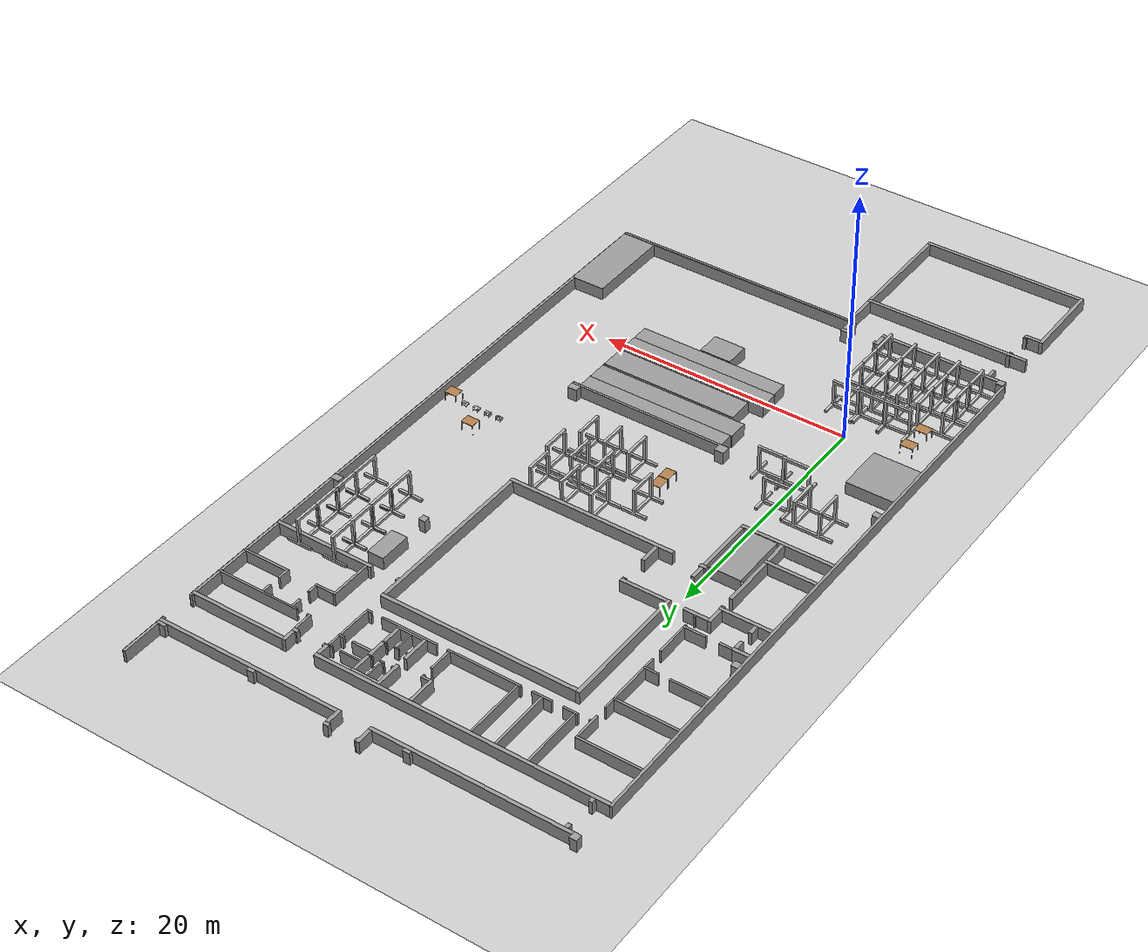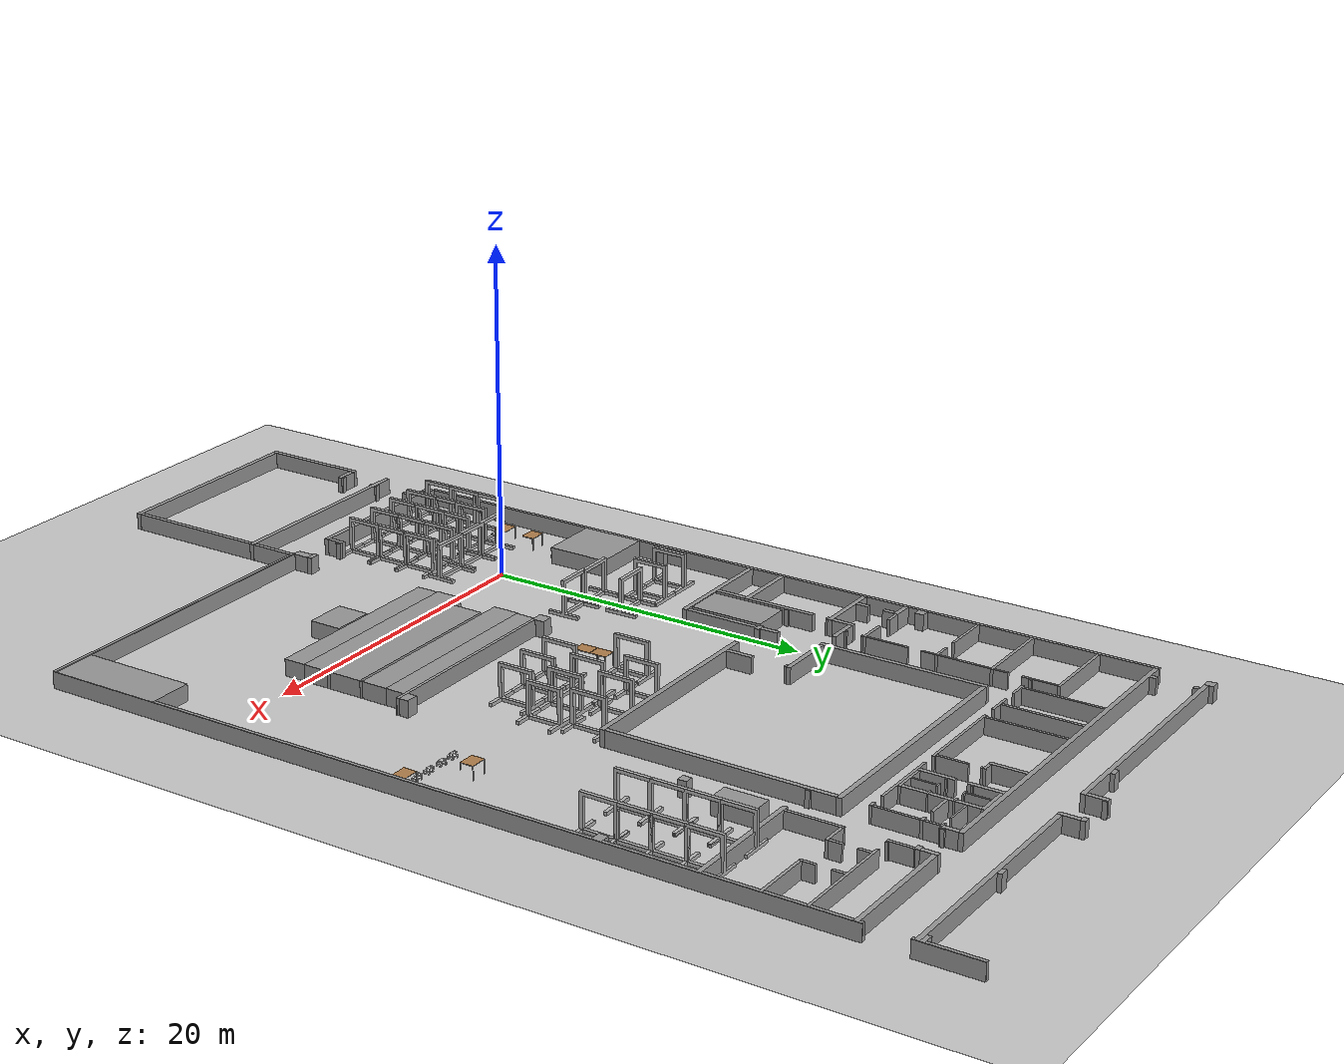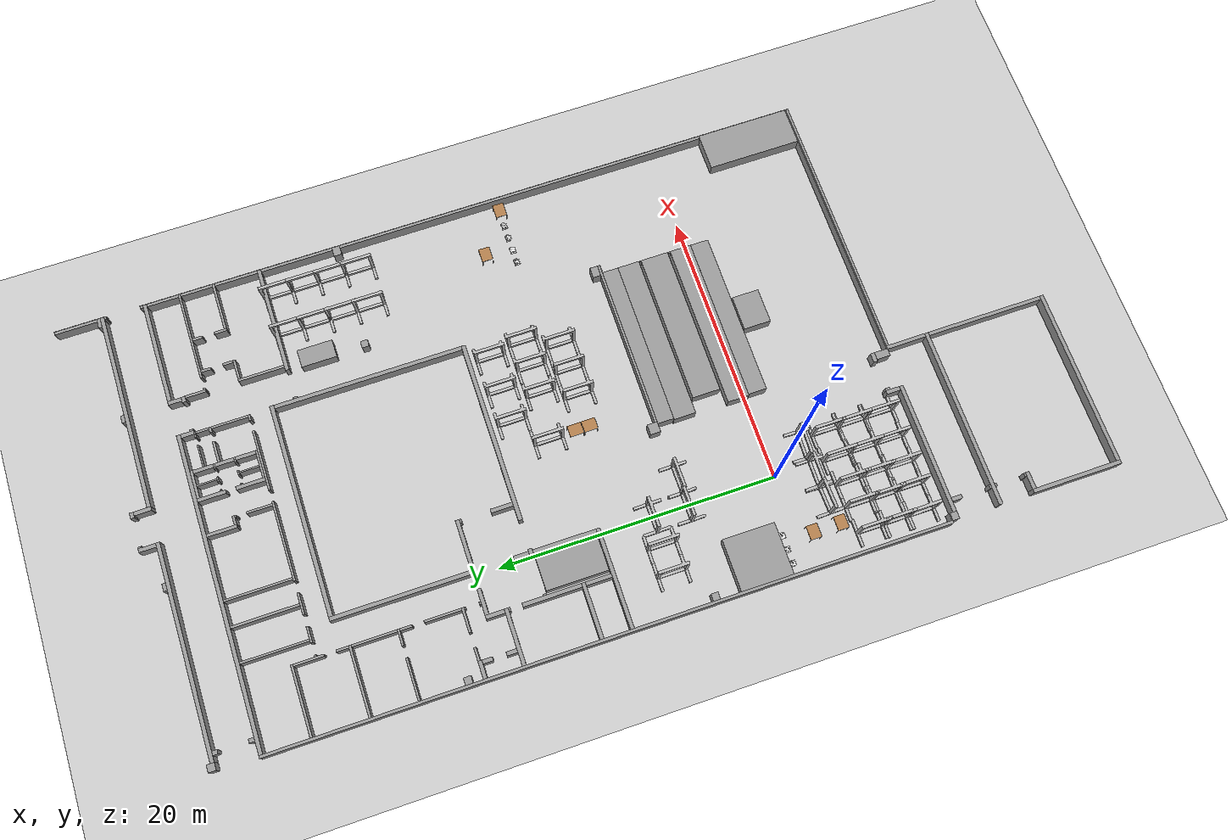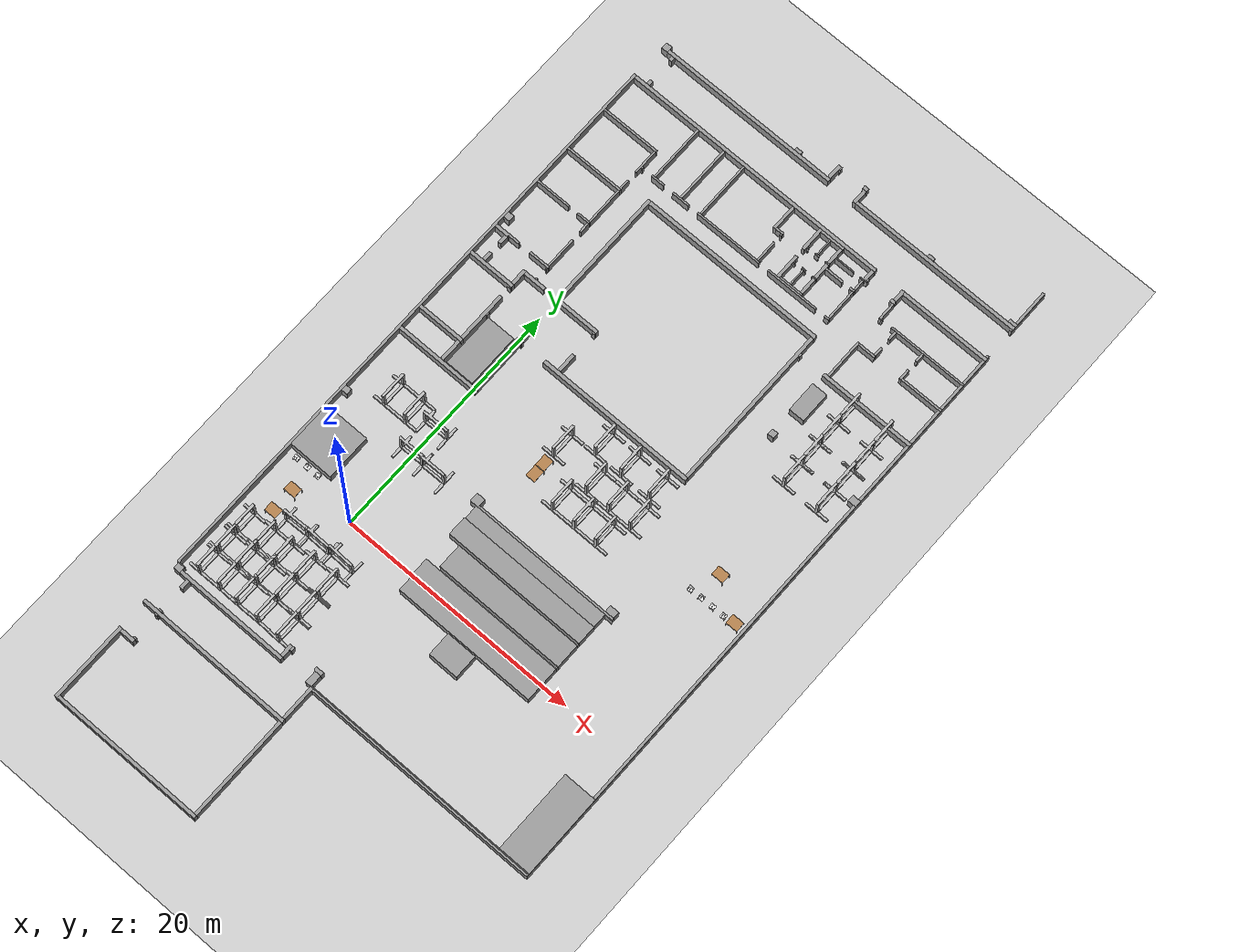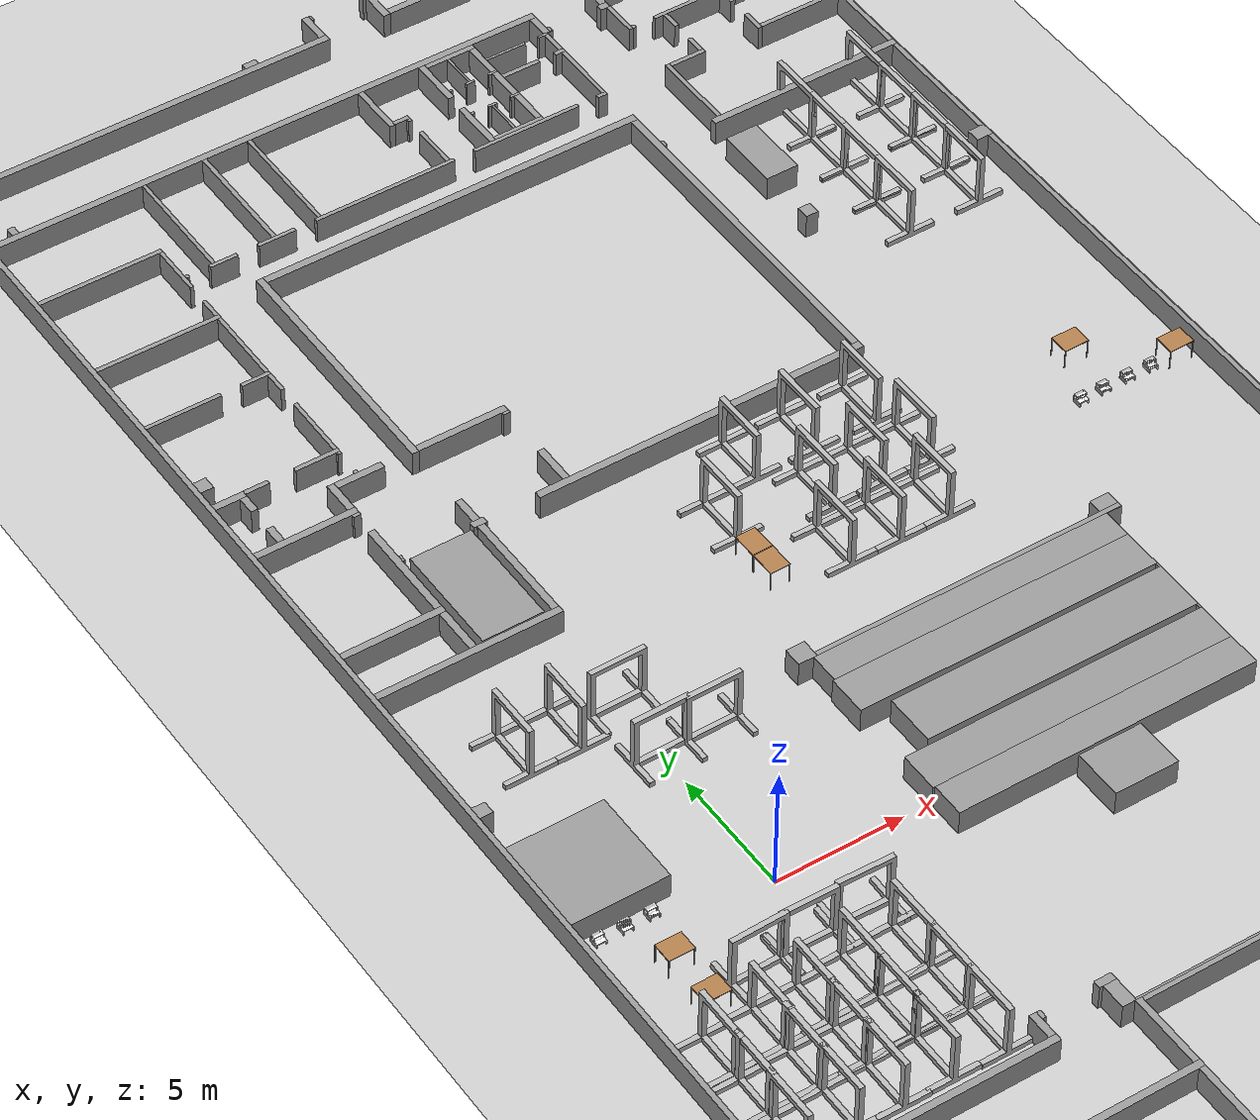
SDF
<sdf version="1.4">
 <world name="default">
  <physics type="ode">
   <gravity>0 0 -9.81</gravity>
   <ode>
    <solver><type>quick</type><iters>20</iters><sor>1</sor></solver>
    <constraints>
     <cfm>0</cfm>
     <erp>0.2</erp>
     <contact_max_correcting_vel>100</contact_max_correcting_vel>
     <contact_surface_layer>0</contact_surface_layer>
    </constraints>
   </ode>
   <real_time_update_rate>1000</real_time_update_rate>
   <max_step_size>0.001</max_step_size>
   <real_time_factor>1</real_time_factor>
   <max_contacts>20</max_contacts>
  </physics>
  <light name="sun" type="directional">
   <pose>0 0 10 0 -0 0</pose>
   <diffuse>0.8 0.8 0.8 1</diffuse>
   <specular>0.2 0.2 0.2 1</specular>
   <attenuation>
    <range>1000</range>
    <constant>0.9</constant>
    <linear>0.01</linear>
    <quadratic>0.001</quadratic>
   </attenuation>
   <direction>0.5 0.1 -0.9</direction>
  </light>
  <model name="ground_plane">
   <static>1</static>
   <link name="link">
    <collision name="collision">
     <geometry><plane><normal>0 0 1</normal><size>100 100</size></plane></geometry>
     <surface><friction><ode><mu>100</mu><mu2>50</mu2></ode></friction></surface>
    </collision>
    <visual name="visual">
     <cast_shadows>0</cast_shadows>
     <geometry><plane><normal>0 0 1</normal><size>100 100</size></plane></geometry>
     <material>
      <script><uri>file://media/materials/scripts/gazebo.material</uri><name>Gazebo/Grey</name></script>
     </material>
    </visual>
    <velocity_decay><linear>0</linear><angular>0</angular></velocity_decay>
   </link>
  </model>
  <model name="walls">
   <static>1</static>
   <link name="Wall_0">
    <collision name="Wall_0_Collision">
     <geometry><box><size>48.5106 0.20426 1</size></box></geometry>
     <pose>36.8426 -0.10213 0.5 0 -0 0</pose>
    </collision>
    <visual name="Wall_0_Visual">
     <geometry><box><size>48.5106 0.20426 1</size></box></geometry>
     <material>
      <script><uri>file://media/materials/scripts/gazebo.material</uri><name>Gazebo/Grey</name></script>
     </material>
     <pose>36.8426 -0.10213 0.5 0 -0 0</pose>
    </visual>
    <velocity_decay><linear>0</linear><angular>0</angular></velocity_decay>
   </link>
   <link name="Wall_1">
    <collision name="Wall_1_Collision">
     <geometry><box><size>6.5617 0.28085 1</size></box></geometry>
     <pose>3.28085 -0.31915 0.5 0 -0 0</pose>
    </collision>
    <visual name="Wall_1_Visual">
     <geometry><box><size>6.5617 0.28085 1</size></box></geometry>
     <material>
      <script><uri>file://media/materials/scripts/gazebo.material</uri><name>Gazebo/Grey</name></script>
     </material>
     <pose>3.28085 -0.31915 0.5 0 -0 0</pose>
    </visual>
    <velocity_decay><linear>0</linear><angular>0</angular></velocity_decay>
   </link>
   <link name="Wall_2">
    <collision name="Wall_2_Collision">
     <geometry><box><size>0.28085 13.0723 1</size></box></geometry>
     <pose>9.02553 -6.71489 0.5 0 -0 0</pose>
    </collision>
    <visual name="Wall_2_Visual">
     <geometry><box><size>0.28085 13.0723 1</size></box></geometry>
     <material>
      <script><uri>file://media/materials/scripts/gazebo.material</uri><name>Gazebo/Grey</name></script>
     </material>
     <pose>9.02553 -6.71489 0.5 0 -0 0</pose>
    </visual>
    <velocity_decay><linear>0</linear><angular>0</angular></velocity_decay>
   </link>
   <link name="Wall_3">
    <collision name="Wall_3_Collision">
     <geometry><box><size>0.51064 0.53617 1</size></box></geometry>
     <pose>12.3319 -0.44681 0.5 0 -0 0</pose>
    </collision>
    <visual name="Wall_3_Visual">
     <geometry><box><size>0.51064 0.53617 1</size></box></geometry>
     <material>
      <script><uri>file://media/materials/scripts/gazebo.material</uri><name>Gazebo/Grey</name></script>
     </material>
     <pose>12.3319 -0.44681 0.5 0 -0 0</pose>
    </visual>
    <velocity_decay><linear>0</linear><angular>0</angular></velocity_decay>
   </link>
   <link name="Wall_4">
    <collision name="Wall_4_Collision">
     <geometry><box><size>0.53617 0.53617 1</size></box></geometry>
     <pose>64.1745 -0.44681 0.5 0 -0 0</pose>
    </collision>
    <visual name="Wall_4_Visual">
     <geometry><box><size>0.53617 0.53617 1</size></box></geometry>
     <material>
      <script><uri>file://media/materials/scripts/gazebo.material</uri><name>Gazebo/Grey</name></script>
     </material>
     <pose>64.1745 -0.44681 0.5 0 -0 0</pose>
    </visual>
    <velocity_decay><linear>0</linear><angular>0</angular></velocity_decay>
   </link>
   <link name="Wall_5">
    <collision name="Wall_5_Collision">
     <geometry><box><size>0.05106 0.51064 1</size></box></geometry>
     <pose>12.6128 -0.45957 0.5 0 -0 0</pose>
    </collision>
    <visual name="Wall_5_Visual">
     <geometry><box><size>0.05106 0.51064 1</size></box></geometry>
     <material>
      <script><uri>file://media/materials/scripts/gazebo.material</uri><name>Gazebo/Grey</name></script>
     </material>
     <pose>12.6128 -0.45957 0.5 0 -0 0</pose>
    </visual>
    <velocity_decay><linear>0</linear><angular>0</angular></velocity_decay>
   </link>
   <link name="Wall_6">
    <collision name="Wall_6_Collision">
     <geometry><box><size>3.77872 3.72766 1</size></box></geometry>
     <pose>25.9915 -2.06809 0.5 0 -0 0</pose>
    </collision>
    <visual name="Wall_6_Visual">
     <geometry><box><size>3.77872 3.72766 1</size></box></geometry>
     <material>
      <script><uri>file://media/materials/scripts/gazebo.material</uri><name>Gazebo/Grey</name></script>
     </material>
     <pose>25.9915 -2.06809 0.5 0 -0 0</pose>
    </visual>
    <velocity_decay><linear>0</linear><angular>0</angular></velocity_decay>
   </link>
   <link name="Wall_7">
    <collision name="Wall_7_Collision">
     <geometry><box><size>0.51064 0.51064 1</size></box></geometry>
     <pose>29.617 -0.45957 0.5 0 -0 0</pose>
    </collision>
    <visual name="Wall_7_Visual">
     <geometry><box><size>0.51064 0.51064 1</size></box></geometry>
     <material>
      <script><uri>file://media/materials/scripts/gazebo.material</uri><name>Gazebo/Grey</name></script>
     </material>
     <pose>29.617 -0.45957 0.5 0 -0 0</pose>
    </visual>
    <velocity_decay><linear>0</linear><angular>0</angular></velocity_decay>
   </link>
   <link name="Wall_8">
    <collision name="Wall_8_Collision">
     <geometry><box><size>0.28085 7.14894 1</size></box></geometry>
     <pose>35.5787 -3.77872 0.5 0 -0 0</pose>
    </collision>
    <visual name="Wall_8_Visual">
     <geometry><box><size>0.28085 7.14894 1</size></box></geometry>
     <material>
      <script><uri>file://media/materials/scripts/gazebo.material</uri><name>Gazebo/Grey</name></script>
     </material>
     <pose>35.5787 -3.77872 0.5 0 -0 0</pose>
    </visual>
    <velocity_decay><linear>0</linear><angular>0</angular></velocity_decay>
   </link>
   <link name="Wall_9">
    <collision name="Wall_9_Collision">
     <geometry><box><size>0.28085 3.95745 1</size></box></geometry>
     <pose>37.6979 -2.18298 0.5 0 -0 0</pose>
    </collision>
    <visual name="Wall_9_Visual">
     <geometry><box><size>0.28085 3.95745 1</size></box></geometry>
     <material>
      <script><uri>file://media/materials/scripts/gazebo.material</uri><name>Gazebo/Grey</name></script>
     </material>
     <pose>37.6979 -2.18298 0.5 0 -0 0</pose>
    </visual>
    <velocity_decay><linear>0</linear><angular>0</angular></velocity_decay>
   </link>
   <link name="Wall_10">
    <collision name="Wall_10_Collision">
     <geometry><box><size>0.28085 3.95745 1</size></box></geometry>
     <pose>43.1106 -2.18298 0.5 0 -0 0</pose>
    </collision>
    <visual name="Wall_10_Visual">
     <geometry><box><size>0.28085 3.95745 1</size></box></geometry>
     <material>
      <script><uri>file://media/materials/scripts/gazebo.material</uri><name>Gazebo/Grey</name></script>
     </material>
     <pose>43.1106 -2.18298 0.5 0 -0 0</pose>
    </visual>
    <velocity_decay><linear>0</linear><angular>0</angular></velocity_decay>
   </link>
   <link name="Wall_11">
    <collision name="Wall_11_Collision">
     <geometry><box><size>0.28085 1.22553 1</size></box></geometry>
     <pose>45.7915 -0.81702 0.5 0 -0 0</pose>
    </collision>
    <visual name="Wall_11_Visual">
     <geometry><box><size>0.28085 1.22553 1</size></box></geometry>
     <material>
      <script><uri>file://media/materials/scripts/gazebo.material</uri><name>Gazebo/Grey</name></script>
     </material>
     <pose>45.7915 -0.81702 0.5 0 -0 0</pose>
    </visual>
    <velocity_decay><linear>0</linear><angular>0</angular></velocity_decay>
   </link>
   <link name="Wall_12">
    <collision name="Wall_12_Collision">
     <geometry><box><size>0.53617 0.51064 1</size></box></geometry>
     <pose>46.8894 -0.45957 0.5 0 -0 0</pose>
    </collision>
    <visual name="Wall_12_Visual">
     <geometry><box><size>0.53617 0.51064 1</size></box></geometry>
     <material>
      <script><uri>file://media/materials/scripts/gazebo.material</uri><name>Gazebo/Grey</name></script>
     </material>
     <pose>46.8894 -0.45957 0.5 0 -0 0</pose>
    </visual>
    <velocity_decay><linear>0</linear><angular>0</angular></velocity_decay>
   </link>
   <link name="Wall_13">
    <collision name="Wall_13_Collision">
     <geometry><box><size>0.15319 2.9617 1</size></box></geometry>
     <pose>50.2979 -1.68511 0.5 0 -0 0</pose>
    </collision>
    <visual name="Wall_13_Visual">
     <geometry><box><size>0.15319 2.9617 1</size></box></geometry>
     <material>
      <script><uri>file://media/materials/scripts/gazebo.material</uri><name>Gazebo/Grey</name></script>
     </material>
     <pose>50.2979 -1.68511 0.5 0 -0 0</pose>
    </visual>
    <velocity_decay><linear>0</linear><angular>0</angular></velocity_decay>
   </link>
   <link name="Wall_14">
    <collision name="Wall_14_Collision">
     <geometry><box><size>0.17872 4.92766 1</size></box></geometry>
     <pose>53.6298 -2.66809 0.5 0 -0 0</pose>
    </collision>
    <visual name="Wall_14_Visual">
     <geometry><box><size>0.17872 4.92766 1</size></box></geometry>
     <material>
      <script><uri>file://media/materials/scripts/gazebo.material</uri><name>Gazebo/Grey</name></script>
     </material>
     <pose>53.6298 -2.66809 0.5 0 -0 0</pose>
    </visual>
    <velocity_decay><linear>0</linear><angular>0</angular></velocity_decay>
   </link>
   <link name="Wall_15">
    <collision name="Wall_15_Collision">
     <geometry><box><size>0.17872 4.92766 1</size></box></geometry>
     <pose>57.5872 -2.66809 0.5 0 -0 0</pose>
    </collision>
    <visual name="Wall_15_Visual">
     <geometry><box><size>0.17872 4.92766 1</size></box></geometry>
     <material>
      <script><uri>file://media/materials/scripts/gazebo.material</uri><name>Gazebo/Grey</name></script>
     </material>
     <pose>57.5872 -2.66809 0.5 0 -0 0</pose>
    </visual>
    <velocity_decay><linear>0</linear><angular>0</angular></velocity_decay>
   </link>
   <link name="Wall_16">
    <collision name="Wall_16_Collision">
     <geometry><box><size>0.28085 22.5702 1</size></box></geometry>
     <pose>60.9575 -11.4894 0.5 0 -0 0</pose>
    </collision>
    <visual name="Wall_16_Visual">
     <geometry><box><size>0.28085 22.5702 1</size></box></geometry>
     <material>
      <script><uri>file://media/materials/scripts/gazebo.material</uri><name>Gazebo/Grey</name></script>
     </material>
     <pose>60.9575 -11.4894 0.5 0 -0 0</pose>
    </visual>
    <velocity_decay><linear>0</linear><angular>0</angular></velocity_decay>
   </link>
   <link name="Wall_17">
    <collision name="Wall_17_Collision">
     <geometry><box><size>0.28085 12.7915 1</size></box></geometry>
     <pose>0.14043 -6.85532 0.5 0 -0 0</pose>
    </collision>
    <visual name="Wall_17_Visual">
     <geometry><box><size>0.28085 12.7915 1</size></box></geometry>
     <material>
      <script><uri>file://media/materials/scripts/gazebo.material</uri><name>Gazebo/Grey</name></script>
     </material>
     <pose>0.14043 -6.85532 0.5 0 -0 0</pose>
    </visual>
    <velocity_decay><linear>0</linear><angular>0</angular></velocity_decay>
   </link>
   <link name="Wall_18">
    <collision name="Wall_18_Collision">
     <geometry><box><size>0.28085 1.22553 1</size></box></geometry>
     <pose>6.42128 -1.07234 0.5 0 -0 0</pose>
    </collision>
    <visual name="Wall_18_Visual">
     <geometry><box><size>0.28085 1.22553 1</size></box></geometry>
     <material>
      <script><uri>file://media/materials/scripts/gazebo.material</uri><name>Gazebo/Grey</name></script>
     </material>
     <pose>6.42128 -1.07234 0.5 0 -0 0</pose>
    </visual>
    <velocity_decay><linear>0</linear><angular>0</angular></velocity_decay>
   </link>
   <link name="Wall_19">
    <collision name="Wall_19_Collision">
     <geometry><box><size>0.28085 9.47234 1</size></box></geometry>
     <pose>12.217 -5.45106 0.5 0 -0 0</pose>
    </collision>
    <visual name="Wall_19_Visual">
     <geometry><box><size>0.28085 9.47234 1</size></box></geometry>
     <material>
      <script><uri>file://media/materials/scripts/gazebo.material</uri><name>Gazebo/Grey</name></script>
     </material>
     <pose>12.217 -5.45106 0.5 0 -0 0</pose>
    </visual>
    <velocity_decay><linear>0</linear><angular>0</angular></velocity_decay>
   </link>
   <link name="Wall_20">
    <collision name="Wall_20_Collision">
     <geometry><box><size>0.28085 15.166 1</size></box></geometry>
     <pose>64.0468 -8.29787 0.5 0 -0 0</pose>
    </collision>
    <visual name="Wall_20_Visual">
     <geometry><box><size>0.28085 15.166 1</size></box></geometry>
     <material>
      <script><uri>file://media/materials/scripts/gazebo.material</uri><name>Gazebo/Grey</name></script>
     </material>
     <pose>64.0468 -8.29787 0.5 0 -0 0</pose>
    </visual>
    <velocity_decay><linear>0</linear><angular>0</angular></velocity_decay>
   </link>
   <link name="Wall_21">
    <collision name="Wall_21_Collision">
     <geometry><box><size>0.74043 0.28085 1</size></box></geometry>
     <pose>43.6213 -1.28936 0.5 0 -0 0</pose>
    </collision>
    <visual name="Wall_21_Visual">
     <geometry><box><size>0.74043 0.28085 1</size></box></geometry>
     <material>
      <script><uri>file://media/materials/scripts/gazebo.material</uri><name>Gazebo/Grey</name></script>
     </material>
     <pose>43.6213 -1.28936 0.5 0 -0 0</pose>
    </visual>
    <velocity_decay><linear>0</linear><angular>0</angular></velocity_decay>
   </link>
   <link name="Wall_22">
    <collision name="Wall_22_Collision">
     <geometry><box><size>0.71489 0.28085 1</size></box></geometry>
     <pose>45.2936 -1.28936 0.5 0 -0 0</pose>
    </collision>
    <visual name="Wall_22_Visual">
     <geometry><box><size>0.71489 0.28085 1</size></box></geometry>
     <material>
      <script><uri>file://media/materials/scripts/gazebo.material</uri><name>Gazebo/Grey</name></script>
     </material>
     <pose>45.2936 -1.28936 0.5 0 -0 0</pose>
    </visual>
    <velocity_decay><linear>0</linear><angular>0</angular></velocity_decay>
   </link>
   <link name="Wall_23">
    <collision name="Wall_23_Collision">
     <geometry><box><size>0.38298 0.28085 1</size></box></geometry>
     <pose>61.2894 -1.28936 0.5 0 -0 0</pose>
    </collision>
    <visual name="Wall_23_Visual">
     <geometry><box><size>0.38298 0.28085 1</size></box></geometry>
     <material>
      <script><uri>file://media/materials/scripts/gazebo.material</uri><name>Gazebo/Grey</name></script>
     </material>
     <pose>61.2894 -1.28936 0.5 0 -0 0</pose>
    </visual>
    <velocity_decay><linear>0</linear><angular>0</angular></velocity_decay>
   </link>
   <link name="Wall_24">
    <collision name="Wall_24_Collision">
     <geometry><box><size>0.35745 0.28085 1</size></box></geometry>
     <pose>63.7277 -1.28936 0.5 0 -0 0</pose>
    </collision>
    <visual name="Wall_24_Visual">
     <geometry><box><size>0.35745 0.28085 1</size></box></geometry>
     <material>
      <script><uri>file://media/materials/scripts/gazebo.material</uri><name>Gazebo/Grey</name></script>
     </material>
     <pose>63.7277 -1.28936 0.5 0 -0 0</pose>
    </visual>
    <velocity_decay><linear>0</linear><angular>0</angular></velocity_decay>
   </link>
   <link name="Wall_25">
    <collision name="Wall_25_Collision">
     <geometry><box><size>0.12766 0.28085 1</size></box></geometry>
     <pose>6.62553 -1.54468 0.5 0 -0 0</pose>
    </collision>
    <visual name="Wall_25_Visual">
     <geometry><box><size>0.12766 0.28085 1</size></box></geometry>
     <material>
      <script><uri>file://media/materials/scripts/gazebo.material</uri><name>Gazebo/Grey</name></script>
     </material>
     <pose>6.62553 -1.54468 0.5 0 -0 0</pose>
    </visual>
    <velocity_decay><linear>0</linear><angular>0</angular></velocity_decay>
   </link>
   <link name="Wall_26">
    <collision name="Wall_26_Collision">
     <geometry><box><size>0.12766 0.28085 1</size></box></geometry>
     <pose>8.82128 -1.54468 0.5 0 -0 0</pose>
    </collision>
    <visual name="Wall_26_Visual">
     <geometry><box><size>0.12766 0.28085 1</size></box></geometry>
     <material>
      <script><uri>file://media/materials/scripts/gazebo.material</uri><name>Gazebo/Grey</name></script>
     </material>
     <pose>8.82128 -1.54468 0.5 0 -0 0</pose>
    </visual>
    <velocity_decay><linear>0</linear><angular>0</angular></velocity_decay>
   </link>
   <link name="Wall_27">
    <collision name="Wall_27_Collision">
     <geometry><box><size>0.12766 0.28085 1</size></box></geometry>
     <pose>9.22979 -1.54468 0.5 0 -0 0</pose>
    </collision>
    <visual name="Wall_27_Visual">
     <geometry><box><size>0.12766 0.28085 1</size></box></geometry>
     <material>
      <script><uri>file://media/materials/scripts/gazebo.material</uri><name>Gazebo/Grey</name></script>
     </material>
     <pose>9.22979 -1.54468 0.5 0 -0 0</pose>
    </visual>
    <velocity_decay><linear>0</linear><angular>0</angular></velocity_decay>
   </link>
   <link name="Wall_28">
    <collision name="Wall_28_Collision">
     <geometry><box><size>0.74043 0.28085 1</size></box></geometry>
     <pose>11.7064 -1.54468 0.5 0 -0 0</pose>
    </collision>
    <visual name="Wall_28_Visual">
     <geometry><box><size>0.74043 0.28085 1</size></box></geometry>
     <material>
      <script><uri>file://media/materials/scripts/gazebo.material</uri><name>Gazebo/Grey</name></script>
     </material>
     <pose>11.7064 -1.54468 0.5 0 -0 0</pose>
    </visual>
    <velocity_decay><linear>0</linear><angular>0</angular></velocity_decay>
   </link>
   <link name="Wall_29">
    <collision name="Wall_29_Collision">
     <geometry><box><size>0.17872 0.94468 1</size></box></geometry>
     <pose>45.8426 -1.90213 0.5 0 -0 0</pose>
    </collision>
    <visual name="Wall_29_Visual">
     <geometry><box><size>0.17872 0.94468 1</size></box></geometry>
     <material>
      <script><uri>file://media/materials/scripts/gazebo.material</uri><name>Gazebo/Grey</name></script>
     </material>
     <pose>45.8426 -1.90213 0.5 0 -0 0</pose>
    </visual>
    <velocity_decay><linear>0</linear><angular>0</angular></velocity_decay>
   </link>
   <link name="Wall_30">
    <collision name="Wall_30_Collision">
     <geometry><box><size>0.17872 1.73617 1</size></box></geometry>
     <pose>45.8426 -4.26383 0.5 0 -0 0</pose>
    </collision>
    <visual name="Wall_30_Visual">
     <geometry><box><size>0.17872 1.73617 1</size></box></geometry>
     <material>
      <script><uri>file://media/materials/scripts/gazebo.material</uri><name>Gazebo/Grey</name></script>
     </material>
     <pose>45.8426 -4.26383 0.5 0 -0 0</pose>
    </visual>
    <velocity_decay><linear>0</linear><angular>0</angular></velocity_decay>
   </link>
   <link name="Wall_31">
    <collision name="Wall_31_Collision">
     <geometry><box><size>1.8383 0.28085 1</size></box></geometry>
     <pose>36.6383 -4.02128 0.5 0 -0 0</pose>
    </collision>
    <visual name="Wall_31_Visual">
     <geometry><box><size>1.8383 0.28085 1</size></box></geometry>
     <material>
      <script><uri>file://media/materials/scripts/gazebo.material</uri><name>Gazebo/Grey</name></script>
     </material>
     <pose>36.6383 -4.02128 0.5 0 -0 0</pose>
    </visual>
    <velocity_decay><linear>0</linear><angular>0</angular></velocity_decay>
   </link>
   <link name="Wall_32">
    <collision name="Wall_32_Collision">
     <geometry><box><size>4.1617 0.28085 1</size></box></geometry>
     <pose>39.9192 -4.02128 0.5 0 -0 0</pose>
    </collision>
    <visual name="Wall_32_Visual">
     <geometry><box><size>4.1617 0.28085 1</size></box></geometry>
     <material>
      <script><uri>file://media/materials/scripts/gazebo.material</uri><name>Gazebo/Grey</name></script>
     </material>
     <pose>39.9192 -4.02128 0.5 0 -0 0</pose>
    </visual>
    <velocity_decay><linear>0</linear><angular>0</angular></velocity_decay>
   </link>
   <link name="Wall_33">
    <collision name="Wall_33_Collision">
     <geometry><box><size>0.12766 0.28085 1</size></box></geometry>
     <pose>42.9064 -4.02128 0.5 0 -0 0</pose>
    </collision>
    <visual name="Wall_33_Visual">
     <geometry><box><size>0.12766 0.28085 1</size></box></geometry>
     <material>
      <script><uri>file://media/materials/scripts/gazebo.material</uri><name>Gazebo/Grey</name></script>
     </material>
     <pose>42.9064 -4.02128 0.5 0 -0 0</pose>
    </visual>
    <velocity_decay><linear>0</linear><angular>0</angular></velocity_decay>
   </link>
   <link name="Wall_34">
    <collision name="Wall_34_Collision">
     <geometry><box><size>1.32766 0.28085 1</size></box></geometry>
     <pose>43.9149 -4.02128 0.5 0 -0 0</pose>
    </collision>
    <visual name="Wall_34_Visual">
     <geometry><box><size>1.32766 0.28085 1</size></box></geometry>
     <material>
      <script><uri>file://media/materials/scripts/gazebo.material</uri><name>Gazebo/Grey</name></script>
     </material>
     <pose>43.9149 -4.02128 0.5 0 -0 0</pose>
    </visual>
    <velocity_decay><linear>0</linear><angular>0</angular></velocity_decay>
   </link>
   <link name="Wall_35">
    <collision name="Wall_35_Collision">
     <geometry><box><size>0.15319 1.14894 1</size></box></geometry>
     <pose>50.2979 -4.55745 0.5 0 -0 0</pose>
    </collision>
    <visual name="Wall_35_Visual">
     <geometry><box><size>0.15319 1.14894 1</size></box></geometry>
     <material>
      <script><uri>file://media/materials/scripts/gazebo.material</uri><name>Gazebo/Grey</name></script>
     </material>
     <pose>50.2979 -4.55745 0.5 0 -0 0</pose>
    </visual>
    <velocity_decay><linear>0</linear><angular>0</angular></velocity_decay>
   </link>
   <link name="Wall_36">
    <collision name="Wall_36_Collision">
     <geometry><box><size>0.28085 0.10213 1</size></box></geometry>
     <pose>40.3787 -4.21277 0.5 0 -0 0</pose>
    </collision>
    <visual name="Wall_36_Visual">
     <geometry><box><size>0.28085 0.10213 1</size></box></geometry>
     <material>
      <script><uri>file://media/materials/scripts/gazebo.material</uri><name>Gazebo/Grey</name></script>
     </material>
     <pose>40.3787 -4.21277 0.5 0 -0 0</pose>
    </visual>
    <velocity_decay><linear>0</linear><angular>0</angular></velocity_decay>
   </link>
   <link name="Wall_37">
    <collision name="Wall_37_Collision">
     <geometry><box><size>0.28085 1.8383 1</size></box></geometry>
     <pose>44.4383 -5.08085 0.5 0 -0 0</pose>
    </collision>
    <visual name="Wall_37_Visual">
     <geometry><box><size>0.28085 1.8383 1</size></box></geometry>
     <material>
      <script><uri>file://media/materials/scripts/gazebo.material</uri><name>Gazebo/Grey</name></script>
     </material>
     <pose>44.4383 -5.08085 0.5 0 -0 0</pose>
    </visual>
    <velocity_decay><linear>0</linear><angular>0</angular></velocity_decay>
   </link>
   <link name="Wall_38">
    <collision name="Wall_38_Collision">
     <geometry><box><size>4.44255 2.4 1</size></box></geometry>
     <pose>37.9915 -5.61702 0.5 0 -0 0</pose>
    </collision>
    <visual name="Wall_38_Visual">
     <geometry><box><size>4.44255 2.4 1</size></box></geometry>
     <material>
      <script><uri>file://media/materials/scripts/gazebo.material</uri><name>Gazebo/Grey</name></script>
     </material>
     <pose>37.9915 -5.61702 0.5 0 -0 0</pose>
    </visual>
    <velocity_decay><linear>0</linear><angular>0</angular></velocity_decay>
   </link>
   <link name="Wall_39">
    <collision name="Wall_39_Collision">
     <geometry><box><size>0.12766 0.15319 1</size></box></geometry>
     <pose>44.6425 -5.05532 0.5 0 -0 0</pose>
    </collision>
    <visual name="Wall_39_Visual">
     <geometry><box><size>0.12766 0.15319 1</size></box></geometry>
     <material>
      <script><uri>file://media/materials/scripts/gazebo.material</uri><name>Gazebo/Grey</name></script>
     </material>
     <pose>44.6425 -5.05532 0.5 0 -0 0</pose>
    </visual>
    <velocity_decay><linear>0</linear><angular>0</angular></velocity_decay>
   </link>
   <link name="Wall_40">
    <collision name="Wall_40_Collision">
     <geometry><box><size>0.10213 0.15319 1</size></box></geometry>
     <pose>45.7021 -5.05532 0.5 0 -0 0</pose>
    </collision>
    <visual name="Wall_40_Visual">
     <geometry><box><size>0.10213 0.15319 1</size></box></geometry>
     <material>
      <script><uri>file://media/materials/scripts/gazebo.material</uri><name>Gazebo/Grey</name></script>
     </material>
     <pose>45.7021 -5.05532 0.5 0 -0 0</pose>
    </visual>
    <velocity_decay><linear>0</linear><angular>0</angular></velocity_decay>
   </link>
   <link name="Wall_41">
    <collision name="Wall_41_Collision">
     <geometry><box><size>2.60426 0.15319 1</size></box></geometry>
     <pose>47.234 -5.05532 0.5 0 -0 0</pose>
    </collision>
    <visual name="Wall_41_Visual">
     <geometry><box><size>2.60426 0.15319 1</size></box></geometry>
     <material>
      <script><uri>file://media/materials/scripts/gazebo.material</uri><name>Gazebo/Grey</name></script>
     </material>
     <pose>47.234 -5.05532 0.5 0 -0 0</pose>
    </visual>
    <velocity_decay><linear>0</linear><angular>0</angular></velocity_decay>
   </link>
   <link name="Wall_42">
    <collision name="Wall_42_Collision">
     <geometry><box><size>0.86809 0.15319 1</size></box></geometry>
     <pose>49.7872 -5.05532 0.5 0 -0 0</pose>
    </collision>
    <visual name="Wall_42_Visual">
     <geometry><box><size>0.86809 0.15319 1</size></box></geometry>
     <material>
      <script><uri>file://media/materials/scripts/gazebo.material</uri><name>Gazebo/Grey</name></script>
     </material>
     <pose>49.7872 -5.05532 0.5 0 -0 0</pose>
    </visual>
    <velocity_decay><linear>0</linear><angular>0</angular></velocity_decay>
   </link>
   <link name="Wall_43">
    <collision name="Wall_43_Collision">
     <geometry><box><size>3.16596 0.15319 1</size></box></geometry>
     <pose>51.9575 -5.05532 0.5 0 -0 0</pose>
    </collision>
    <visual name="Wall_43_Visual">
     <geometry><box><size>3.16596 0.15319 1</size></box></geometry>
     <material>
      <script><uri>file://media/materials/scripts/gazebo.material</uri><name>Gazebo/Grey</name></script>
     </material>
     <pose>51.9575 -5.05532 0.5 0 -0 0</pose>
    </visual>
    <velocity_decay><linear>0</linear><angular>0</angular></velocity_decay>
   </link>
   <link name="Wall_44">
    <collision name="Wall_44_Collision">
     <geometry><box><size>0.86809 0.15319 1</size></box></geometry>
     <pose>54.1532 -5.05532 0.5 0 -0 0</pose>
    </collision>
    <visual name="Wall_44_Visual">
     <geometry><box><size>0.86809 0.15319 1</size></box></geometry>
     <material>
      <script><uri>file://media/materials/scripts/gazebo.material</uri><name>Gazebo/Grey</name></script>
     </material>
     <pose>54.1532 -5.05532 0.5 0 -0 0</pose>
    </visual>
    <velocity_decay><linear>0</linear><angular>0</angular></velocity_decay>
   </link>
   <link name="Wall_45">
    <collision name="Wall_45_Collision">
     <geometry><box><size>2.09362 0.15319 1</size></box></geometry>
     <pose>56.4511 -5.05532 0.5 0 -0 0</pose>
    </collision>
    <visual name="Wall_45_Visual">
     <geometry><box><size>2.09362 0.15319 1</size></box></geometry>
     <material>
      <script><uri>file://media/materials/scripts/gazebo.material</uri><name>Gazebo/Grey</name></script>
     </material>
     <pose>56.4511 -5.05532 0.5 0 -0 0</pose>
    </visual>
    <velocity_decay><linear>0</linear><angular>0</angular></velocity_decay>
   </link>
   <link name="Wall_46">
    <collision name="Wall_46_Collision">
     <geometry><box><size>0.15319 0.12766 1</size></box></geometry>
     <pose>55.966 -5.19574 0.5 0 -0 0</pose>
    </collision>
    <visual name="Wall_46_Visual">
     <geometry><box><size>0.15319 0.12766 1</size></box></geometry>
     <material>
      <script><uri>file://media/materials/scripts/gazebo.material</uri><name>Gazebo/Grey</name></script>
     </material>
     <pose>55.966 -5.19574 0.5 0 -0 0</pose>
    </visual>
    <velocity_decay><linear>0</linear><angular>0</angular></velocity_decay>
   </link>
   <link name="Wall_47">
    <collision name="Wall_47_Collision">
     <geometry><box><size>0.15319 1.1234 1</size></box></geometry>
     <pose>55.966 -6.66383 0.5 0 -0 0</pose>
    </collision>
    <visual name="Wall_47_Visual">
     <geometry><box><size>0.15319 1.1234 1</size></box></geometry>
     <material>
      <script><uri>file://media/materials/scripts/gazebo.material</uri><name>Gazebo/Grey</name></script>
     </material>
     <pose>55.966 -6.66383 0.5 0 -0 0</pose>
    </visual>
    <velocity_decay><linear>0</linear><angular>0</angular></velocity_decay>
   </link>
   <link name="Wall_48">
    <collision name="Wall_48_Collision">
     <geometry><box><size>4.77447 0.15319 1</size></box></geometry>
     <pose>58.4298 -6.30638 0.5 0 -0 0</pose>
    </collision>
    <visual name="Wall_48_Visual">
     <geometry><box><size>4.77447 0.15319 1</size></box></geometry>
     <material>
      <script><uri>file://media/materials/scripts/gazebo.material</uri><name>Gazebo/Grey</name></script>
     </material>
     <pose>58.4298 -6.30638 0.5 0 -0 0</pose>
    </visual>
    <velocity_decay><linear>0</linear><angular>0</angular></velocity_decay>
   </link>
   <link name="Wall_49">
    <collision name="Wall_49_Collision">
     <geometry><box><size>0.28085 0.53617 1</size></box></geometry>
     <pose>40.3787 -7.21277 0.5 0 -0 0</pose>
    </collision>
    <visual name="Wall_49_Visual">
     <geometry><box><size>0.28085 0.53617 1</size></box></geometry>
     <material>
      <script><uri>file://media/materials/scripts/gazebo.material</uri><name>Gazebo/Grey</name></script>
     </material>
     <pose>40.3787 -7.21277 0.5 0 -0 0</pose>
    </visual>
    <velocity_decay><linear>0</linear><angular>0</angular></velocity_decay>
   </link>
   <link name="Wall_50">
    <collision name="Wall_50_Collision">
     <geometry><box><size>4.51915 0.28085 1</size></box></geometry>
     <pose>37.9787 -7.21277 0.5 0 -0 0</pose>
    </collision>
    <visual name="Wall_50_Visual">
     <geometry><box><size>4.51915 0.28085 1</size></box></geometry>
     <material>
      <script><uri>file://media/materials/scripts/gazebo.material</uri><name>Gazebo/Grey</name></script>
     </material>
     <pose>37.9787 -7.21277 0.5 0 -0 0</pose>
    </visual>
    <velocity_decay><linear>0</linear><angular>0</angular></velocity_decay>
   </link>
   <link name="Wall_51">
    <collision name="Wall_51_Collision">
     <geometry><box><size>1.09787 0.28085 1</size></box></geometry>
     <pose>41.0681 -7.21277 0.5 0 -0 0</pose>
    </collision>
    <visual name="Wall_51_Visual">
     <geometry><box><size>1.09787 0.28085 1</size></box></geometry>
     <material>
      <script><uri>file://media/materials/scripts/gazebo.material</uri><name>Gazebo/Grey</name></script>
     </material>
     <pose>41.0681 -7.21277 0.5 0 -0 0</pose>
    </visual>
    <velocity_decay><linear>0</linear><angular>0</angular></velocity_decay>
   </link>
   <link name="Wall_52">
    <collision name="Wall_52_Collision">
     <geometry><box><size>10.1617 0.28085 1</size></box></geometry>
     <pose>49.3787 -7.21277 0.5 0 -0 0</pose>
    </collision>
    <visual name="Wall_52_Visual">
     <geometry><box><size>10.1617 0.28085 1</size></box></geometry>
     <material>
      <script><uri>file://media/materials/scripts/gazebo.material</uri><name>Gazebo/Grey</name></script>
     </material>
     <pose>49.3787 -7.21277 0.5 0 -0 0</pose>
    </visual>
    <velocity_decay><linear>0</linear><angular>0</angular></velocity_decay>
   </link>
   <link name="Wall_53">
    <collision name="Wall_53_Collision">
     <geometry><box><size>0.02553 0.12766 1</size></box></geometry>
     <pose>40.2255 -7.41702 0.5 0 -0 0</pose>
    </collision>
    <visual name="Wall_53_Visual">
     <geometry><box><size>0.02553 0.12766 1</size></box></geometry>
     <material>
      <script><uri>file://media/materials/scripts/gazebo.material</uri><name>Gazebo/Grey</name></script>
     </material>
     <pose>40.2255 -7.41702 0.5 0 -0 0</pose>
    </visual>
    <velocity_decay><linear>0</linear><angular>0</angular></velocity_decay>
   </link>
   <link name="Wall_54">
    <collision name="Wall_54_Collision">
     <geometry><box><size>0.28085 3.57447 1</size></box></geometry>
     <pose>44.4383 -9.14043 0.5 0 -0 0</pose>
    </collision>
    <visual name="Wall_54_Visual">
     <geometry><box><size>0.28085 3.57447 1</size></box></geometry>
     <material>
      <script><uri>file://media/materials/scripts/gazebo.material</uri><name>Gazebo/Grey</name></script>
     </material>
     <pose>44.4383 -9.14043 0.5 0 -0 0</pose>
    </visual>
    <velocity_decay><linear>0</linear><angular>0</angular></velocity_decay>
   </link>
   <link name="Wall_55">
    <collision name="Wall_55_Collision">
     <geometry><box><size>0.30638 15.4213 1</size></box></geometry>
     <pose>54.3064 -15.0638 0.5 0 -0 0</pose>
    </collision>
    <visual name="Wall_55_Visual">
     <geometry><box><size>0.30638 15.4213 1</size></box></geometry>
     <material>
      <script><uri>file://media/materials/scripts/gazebo.material</uri><name>Gazebo/Grey</name></script>
     </material>
     <pose>54.3064 -15.0638 0.5 0 -0 0</pose>
    </visual>
    <velocity_decay><linear>0</linear><angular>0</angular></velocity_decay>
   </link>
   <link name="Wall_56">
    <collision name="Wall_56_Collision">
     <geometry><box><size>0.15319 1.50638 1</size></box></geometry>
     <pose>55.966 -8.82128 0.5 0 -0 0</pose>
    </collision>
    <visual name="Wall_56_Visual">
     <geometry><box><size>0.15319 1.50638 1</size></box></geometry>
     <material>
      <script><uri>file://media/materials/scripts/gazebo.material</uri><name>Gazebo/Grey</name></script>
     </material>
     <pose>55.966 -8.82128 0.5 0 -0 0</pose>
    </visual>
    <velocity_decay><linear>0</linear><angular>0</angular></velocity_decay>
   </link>
   <link name="Wall_57">
    <collision name="Wall_57_Collision">
     <geometry><box><size>4.77447 0.17872 1</size></box></geometry>
     <pose>58.4298 -8.77021 0.5 0 -0 0</pose>
    </collision>
    <visual name="Wall_57_Visual">
     <geometry><box><size>4.77447 0.17872 1</size></box></geometry>
     <material>
      <script><uri>file://media/materials/scripts/gazebo.material</uri><name>Gazebo/Grey</name></script>
     </material>
     <pose>58.4298 -8.77021 0.5 0 -0 0</pose>
    </visual>
    <velocity_decay><linear>0</linear><angular>0</angular></velocity_decay>
   </link>
   <link name="Wall_58">
    <collision name="Wall_58_Collision">
     <geometry><box><size>0.30638 13.2255 1</size></box></geometry>
     <pose>40.366 -16.1617 0.5 0 -0 0</pose>
    </collision>
    <visual name="Wall_58_Visual">
     <geometry><box><size>0.30638 13.2255 1</size></box></geometry>
     <material>
      <script><uri>file://media/materials/scripts/gazebo.material</uri><name>Gazebo/Grey</name></script>
     </material>
     <pose>40.366 -16.1617 0.5 0 -0 0</pose>
    </visual>
    <velocity_decay><linear>0</linear><angular>0</angular></velocity_decay>
   </link>
   <link name="Wall_59">
    <collision name="Wall_59_Collision">
     <geometry><box><size>1.02128 0.28085 1</size></box></geometry>
     <pose>12.8681 -10.0468 0.5 0 -0 0</pose>
    </collision>
    <visual name="Wall_59_Visual">
     <geometry><box><size>1.02128 0.28085 1</size></box></geometry>
     <material>
      <script><uri>file://media/materials/scripts/gazebo.material</uri><name>Gazebo/Grey</name></script>
     </material>
     <pose>12.8681 -10.0468 0.5 0 -0 0</pose>
    </visual>
    <velocity_decay><linear>0</linear><angular>0</angular></velocity_decay>
   </link>
   <link name="Wall_60">
    <collision name="Wall_60_Collision">
     <geometry><box><size>0.33191 0.15319 1</size></box></geometry>
     <pose>13.2128 -10.2638 0.5 0 -0 0</pose>
    </collision>
    <visual name="Wall_60_Visual">
     <geometry><box><size>0.33191 0.15319 1</size></box></geometry>
     <material>
      <script><uri>file://media/materials/scripts/gazebo.material</uri><name>Gazebo/Grey</name></script>
     </material>
     <pose>13.2128 -10.2638 0.5 0 -0 0</pose>
    </visual>
    <velocity_decay><linear>0</linear><angular>0</angular></velocity_decay>
   </link>
   <link name="Wall_61">
    <collision name="Wall_61_Collision">
     <geometry><box><size>0.15319 5.74468 1</size></box></geometry>
     <pose>55.966 -13.2894 0.5 0 -0 0</pose>
    </collision>
    <visual name="Wall_61_Visual">
     <geometry><box><size>0.15319 5.74468 1</size></box></geometry>
     <material>
      <script><uri>file://media/materials/scripts/gazebo.material</uri><name>Gazebo/Grey</name></script>
     </material>
     <pose>55.966 -13.2894 0.5 0 -0 0</pose>
    </visual>
    <velocity_decay><linear>0</linear><angular>0</angular></velocity_decay>
   </link>
   <link name="Wall_62">
    <collision name="Wall_62_Collision">
     <geometry><box><size>4.77447 0.15319 1</size></box></geometry>
     <pose>58.4298 -10.6213 0.5 0 -0 0</pose>
    </collision>
    <visual name="Wall_62_Visual">
     <geometry><box><size>4.77447 0.15319 1</size></box></geometry>
     <material>
      <script><uri>file://media/materials/scripts/gazebo.material</uri><name>Gazebo/Grey</name></script>
     </material>
     <pose>58.4298 -10.6213 0.5 0 -0 0</pose>
    </visual>
    <velocity_decay><linear>0</linear><angular>0</angular></velocity_decay>
   </link>
   <link name="Wall_63">
    <collision name="Wall_63_Collision">
     <geometry><box><size>1.58298 0.28085 1</size></box></geometry>
     <pose>41.3106 -10.7872 0.5 0 -0 0</pose>
    </collision>
    <visual name="Wall_63_Visual">
     <geometry><box><size>1.58298 0.28085 1</size></box></geometry>
     <material>
      <script><uri>file://media/materials/scripts/gazebo.material</uri><name>Gazebo/Grey</name></script>
     </material>
     <pose>41.3106 -10.7872 0.5 0 -0 0</pose>
    </visual>
    <velocity_decay><linear>0</linear><angular>0</angular></velocity_decay>
   </link>
   <link name="Wall_64">
    <collision name="Wall_64_Collision">
     <geometry><box><size>0.12766 0.28085 1</size></box></geometry>
     <pose>44.234 -10.7872 0.5 0 -0 0</pose>
    </collision>
    <visual name="Wall_64_Visual">
     <geometry><box><size>0.12766 0.28085 1</size></box></geometry>
     <material>
      <script><uri>file://media/materials/scripts/gazebo.material</uri><name>Gazebo/Grey</name></script>
     </material>
     <pose>44.234 -10.7872 0.5 0 -0 0</pose>
    </visual>
    <velocity_decay><linear>0</linear><angular>0</angular></velocity_decay>
   </link>
   <link name="Wall_65">
    <collision name="Wall_65_Collision">
     <geometry><box><size>0.30638 0.66383 1</size></box></geometry>
     <pose>13.2255 -12.7149 0.5 0 -0 0</pose>
    </collision>
    <visual name="Wall_65_Visual">
     <geometry><box><size>0.30638 0.66383 1</size></box></geometry>
     <material>
      <script><uri>file://media/materials/scripts/gazebo.material</uri><name>Gazebo/Grey</name></script>
     </material>
     <pose>13.2255 -12.7149 0.5 0 -0 0</pose>
    </visual>
    <velocity_decay><linear>0</linear><angular>0</angular></velocity_decay>
   </link>
   <link name="Wall_66">
    <collision name="Wall_66_Collision">
     <geometry><box><size>0.74043 0.74043 1</size></box></geometry>
     <pose>29.6298 -12.7787 0.5 0 -0 0</pose>
    </collision>
    <visual name="Wall_66_Visual">
     <geometry><box><size>0.74043 0.74043 1</size></box></geometry>
     <material>
      <script><uri>file://media/materials/scripts/gazebo.material</uri><name>Gazebo/Grey</name></script>
     </material>
     <pose>29.6298 -12.7787 0.5 0 -0 0</pose>
    </visual>
    <velocity_decay><linear>0</linear><angular>0</angular></velocity_decay>
   </link>
   <link name="Wall_67">
    <collision name="Wall_67_Collision">
     <geometry><box><size>0.99574 0.53617 1</size></box></geometry>
     <pose>12.5745 -12.7787 0.5 0 -0 0</pose>
    </collision>
    <visual name="Wall_67_Visual">
     <geometry><box><size>0.99574 0.53617 1</size></box></geometry>
     <material>
      <script><uri>file://media/materials/scripts/gazebo.material</uri><name>Gazebo/Grey</name></script>
     </material>
     <pose>12.5745 -12.7787 0.5 0 -0 0</pose>
    </visual>
    <velocity_decay><linear>0</linear><angular>0</angular></velocity_decay>
   </link>
   <link name="Wall_68">
    <collision name="Wall_68_Collision">
     <geometry><box><size>0.25532 0.53617 1</size></box></geometry>
     <pose>64.3149 -12.7787 0.5 0 -0 0</pose>
    </collision>
    <visual name="Wall_68_Visual">
     <geometry><box><size>0.25532 0.53617 1</size></box></geometry>
     <material>
      <script><uri>file://media/materials/scripts/gazebo.material</uri><name>Gazebo/Grey</name></script>
     </material>
     <pose>64.3149 -12.7787 0.5 0 -0 0</pose>
    </visual>
    <velocity_decay><linear>0</linear><angular>0</angular></velocity_decay>
   </link>
   <link name="Wall_69">
    <collision name="Wall_69_Collision">
     <geometry><box><size>1.55745 11.9745 1</size></box></geometry>
     <pose>23.3234 -18.9064 0.5 0 -0 0</pose>
    </collision>
    <visual name="Wall_69_Visual">
     <geometry><box><size>1.55745 11.9745 1</size></box></geometry>
     <material>
      <script><uri>file://media/materials/scripts/gazebo.material</uri><name>Gazebo/Grey</name></script>
     </material>
     <pose>23.3234 -18.9064 0.5 0 -0 0</pose>
    </visual>
    <velocity_decay><linear>0</linear><angular>0</angular></velocity_decay>
   </link>
   <link name="Wall_70">
    <collision name="Wall_70_Collision">
     <geometry><box><size>1.58298 11.9745 1</size></box></geometry>
     <pose>27.2936 -18.9064 0.5 0 -0 0</pose>
    </collision>
    <visual name="Wall_70_Visual">
     <geometry><box><size>1.58298 11.9745 1</size></box></geometry>
     <material>
      <script><uri>file://media/materials/scripts/gazebo.material</uri><name>Gazebo/Grey</name></script>
     </material>
     <pose>27.2936 -18.9064 0.5 0 -0 0</pose>
    </visual>
    <velocity_decay><linear>0</linear><angular>0</angular></velocity_decay>
   </link>
   <link name="Wall_71">
    <collision name="Wall_71_Collision">
     <geometry><box><size>8.60426 0.25532 1</size></box></geometry>
     <pose>4.58298 -13.1234 0.5 0 -0 0</pose>
    </collision>
    <visual name="Wall_71_Visual">
     <geometry><box><size>8.60426 0.25532 1</size></box></geometry>
     <material>
      <script><uri>file://media/materials/scripts/gazebo.material</uri><name>Gazebo/Grey</name></script>
     </material>
     <pose>4.58298 -13.1234 0.5 0 -0 0</pose>
    </visual>
    <velocity_decay><linear>0</linear><angular>0</angular></velocity_decay>
   </link>
   <link name="Wall_72">
    <collision name="Wall_72_Collision">
     <geometry><box><size>2.91064 0.25532 1</size></box></geometry>
     <pose>10.6213 -13.1234 0.5 0 -0 0</pose>
    </collision>
    <visual name="Wall_72_Visual">
     <geometry><box><size>2.91064 0.25532 1</size></box></geometry>
     <material>
      <script><uri>file://media/materials/scripts/gazebo.material</uri><name>Gazebo/Grey</name></script>
     </material>
     <pose>10.6213 -13.1234 0.5 0 -0 0</pose>
    </visual>
    <velocity_decay><linear>0</linear><angular>0</angular></velocity_decay>
   </link>
   <link name="Wall_73">
    <collision name="Wall_73_Collision">
     <geometry><box><size>1.32766 11.8979 1</size></box></geometry>
     <pose>21.8808 -18.9447 0.5 0 -0 0</pose>
    </collision>
    <visual name="Wall_73_Visual">
     <geometry><box><size>1.32766 11.8979 1</size></box></geometry>
     <material>
      <script><uri>file://media/materials/scripts/gazebo.material</uri><name>Gazebo/Grey</name></script>
     </material>
     <pose>21.8808 -18.9447 0.5 0 -0 0</pose>
    </visual>
    <velocity_decay><linear>0</linear><angular>0</angular></velocity_decay>
   </link>
   <link name="Wall_74">
    <collision name="Wall_74_Collision">
     <geometry><box><size>1.17447 11.8979 1</size></box></geometry>
     <pose>28.6723 -18.9447 0.5 0 -0 0</pose>
    </collision>
    <visual name="Wall_74_Visual">
     <geometry><box><size>1.17447 11.8979 1</size></box></geometry>
     <material>
      <script><uri>file://media/materials/scripts/gazebo.material</uri><name>Gazebo/Grey</name></script>
     </material>
     <pose>28.6723 -18.9447 0.5 0 -0 0</pose>
    </visual>
    <velocity_decay><linear>0</linear><angular>0</angular></velocity_decay>
   </link>
   <link name="Wall_75">
    <collision name="Wall_75_Collision">
     <geometry><box><size>0.0766 19.8894 1</size></box></geometry>
     <pose>12.1149 -22.9915 0.5 0 -0 0</pose>
    </collision>
    <visual name="Wall_75_Visual">
     <geometry><box><size>0.0766 19.8894 1</size></box></geometry>
     <material>
      <script><uri>file://media/materials/scripts/gazebo.material</uri><name>Gazebo/Grey</name></script>
     </material>
     <pose>12.1149 -22.9915 0.5 0 -0 0</pose>
    </visual>
    <velocity_decay><linear>0</linear><angular>0</angular></velocity_decay>
   </link>
   <link name="Wall_76">
    <collision name="Wall_76_Collision">
     <geometry><box><size>0.17872 12.3575 1</size></box></geometry>
     <pose>29.3489 -19.3277 0.5 0 -0 0</pose>
    </collision>
    <visual name="Wall_76_Visual">
     <geometry><box><size>0.17872 12.3575 1</size></box></geometry>
     <material>
      <script><uri>file://media/materials/scripts/gazebo.material</uri><name>Gazebo/Grey</name></script>
     </material>
     <pose>29.3489 -19.3277 0.5 0 -0 0</pose>
    </visual>
    <velocity_decay><linear>0</linear><angular>0</angular></velocity_decay>
   </link>
   <link name="Wall_77">
    <collision name="Wall_77_Collision">
     <geometry><box><size>0.17872 19.6851 1</size></box></geometry>
     <pose>11.9872 -23.0936 0.5 0 -0 0</pose>
    </collision>
    <visual name="Wall_77_Visual">
     <geometry><box><size>0.17872 19.6851 1</size></box></geometry>
     <material>
      <script><uri>file://media/materials/scripts/gazebo.material</uri><name>Gazebo/Grey</name></script>
     </material>
     <pose>11.9872 -23.0936 0.5 0 -0 0</pose>
    </visual>
    <velocity_decay><linear>0</linear><angular>0</angular></velocity_decay>
   </link>
   <link name="Wall_78">
    <collision name="Wall_78_Collision">
     <geometry><box><size>2.01702 10.9021 1</size></box></geometry>
     <pose>25.3149 -19.4426 0.5 0 -0 0</pose>
    </collision>
    <visual name="Wall_78_Visual">
     <geometry><box><size>2.01702 10.9021 1</size></box></geometry>
     <material>
      <script><uri>file://media/materials/scripts/gazebo.material</uri><name>Gazebo/Grey</name></script>
     </material>
     <pose>25.3149 -19.4426 0.5 0 -0 0</pose>
    </visual>
    <velocity_decay><linear>0</linear><angular>0</angular></velocity_decay>
   </link>
   <link name="Wall_79">
    <collision name="Wall_79_Collision">
     <geometry><box><size>2.14468 0.22979 1</size></box></geometry>
     <pose>59.7447 -15.2808 0.5 0 -0 0</pose>
    </collision>
    <visual name="Wall_79_Visual">
     <geometry><box><size>2.14468 0.22979 1</size></box></geometry>
     <material>
      <script><uri>file://media/materials/scripts/gazebo.material</uri><name>Gazebo/Grey</name></script>
     </material>
     <pose>59.7447 -15.2808 0.5 0 -0 0</pose>
    </visual>
    <velocity_decay><linear>0</linear><angular>0</angular></velocity_decay>
   </link>
   <link name="Wall_80">
    <collision name="Wall_80_Collision">
     <geometry><box><size>0.17872 0.6383 1</size></box></geometry>
     <pose>58.7617 -15.7149 0.5 0 -0 0</pose>
    </collision>
    <visual name="Wall_80_Visual">
     <geometry><box><size>0.17872 0.6383 1</size></box></geometry>
     <material>
      <script><uri>file://media/materials/scripts/gazebo.material</uri><name>Gazebo/Grey</name></script>
     </material>
     <pose>58.7617 -15.7149 0.5 0 -0 0</pose>
    </visual>
    <velocity_decay><linear>0</linear><angular>0</angular></velocity_decay>
   </link>
   <link name="Wall_81">
    <collision name="Wall_81_Collision">
     <geometry><box><size>1.22553 0.28085 1</size></box></geometry>
     <pose>64.8 -15.7404 0.5 0 -0 0</pose>
    </collision>
    <visual name="Wall_81_Visual">
     <geometry><box><size>1.22553 0.28085 1</size></box></geometry>
     <material>
      <script><uri>file://media/materials/scripts/gazebo.material</uri><name>Gazebo/Grey</name></script>
     </material>
     <pose>64.8 -15.7404 0.5 0 -0 0</pose>
    </visual>
    <velocity_decay><linear>0</linear><angular>0</angular></velocity_decay>
   </link>
   <link name="Wall_82">
    <collision name="Wall_82_Collision">
     <geometry><box><size>1.81277 0.15319 1</size></box></geometry>
     <pose>56.9489 -15.9574 0.5 0 -0 0</pose>
    </collision>
    <visual name="Wall_82_Visual">
     <geometry><box><size>1.81277 0.15319 1</size></box></geometry>
     <material>
      <script><uri>file://media/materials/scripts/gazebo.material</uri><name>Gazebo/Grey</name></script>
     </material>
     <pose>56.9489 -15.9574 0.5 0 -0 0</pose>
    </visual>
    <velocity_decay><linear>0</linear><angular>0</angular></velocity_decay>
   </link>
   <link name="Wall_83">
    <collision name="Wall_83_Collision">
     <geometry><box><size>0.12766 0.15319 1</size></box></geometry>
     <pose>58.6085 -15.9574 0.5 0 -0 0</pose>
    </collision>
    <visual name="Wall_83_Visual">
     <geometry><box><size>0.12766 0.15319 1</size></box></geometry>
     <material>
      <script><uri>file://media/materials/scripts/gazebo.material</uri><name>Gazebo/Grey</name></script>
     </material>
     <pose>58.6085 -15.9574 0.5 0 -0 0</pose>
    </visual>
    <velocity_decay><linear>0</linear><angular>0</angular></velocity_decay>
   </link>
   <link name="Wall_84">
    <collision name="Wall_84_Collision">
     <geometry><box><size>0.28085 0.10213 1</size></box></geometry>
     <pose>65.2723 -15.9319 0.5 0 -0 0</pose>
    </collision>
    <visual name="Wall_84_Visual">
     <geometry><box><size>0.28085 0.10213 1</size></box></geometry>
     <material>
      <script><uri>file://media/materials/scripts/gazebo.material</uri><name>Gazebo/Grey</name></script>
     </material>
     <pose>65.2723 -15.9319 0.5 0 -0 0</pose>
    </visual>
    <velocity_decay><linear>0</linear><angular>0</angular></velocity_decay>
   </link>
   <link name="Wall_85">
    <collision name="Wall_85_Collision">
     <geometry><box><size>0.15319 4.41702 1</size></box></geometry>
     <pose>55.966 -19.2128 0.5 0 -0 0</pose>
    </collision>
    <visual name="Wall_85_Visual">
     <geometry><box><size>0.15319 4.41702 1</size></box></geometry>
     <material>
      <script><uri>file://media/materials/scripts/gazebo.material</uri><name>Gazebo/Grey</name></script>
     </material>
     <pose>55.966 -19.2128 0.5 0 -0 0</pose>
    </visual>
    <velocity_decay><linear>0</linear><angular>0</angular></velocity_decay>
   </link>
   <link name="Wall_86">
    <collision name="Wall_86_Collision">
     <geometry><box><size>1.96596 2.50213 1</size></box></geometry>
     <pose>20.1319 -18.8681 0.5 0 -0 0</pose>
    </collision>
    <visual name="Wall_86_Visual">
     <geometry><box><size>1.96596 2.50213 1</size></box></geometry>
     <material>
      <script><uri>file://media/materials/scripts/gazebo.material</uri><name>Gazebo/Grey</name></script>
     </material>
     <pose>20.1319 -18.8681 0.5 0 -0 0</pose>
    </visual>
    <velocity_decay><linear>0</linear><angular>0</angular></velocity_decay>
   </link>
   <link name="Wall_87">
    <collision name="Wall_87_Collision">
     <geometry><box><size>2.06809 0.25532 1</size></box></geometry>
     <pose>57.0766 -17.8468 0.5 0 -0 0</pose>
    </collision>
    <visual name="Wall_87_Visual">
     <geometry><box><size>2.06809 0.25532 1</size></box></geometry>
     <material>
      <script><uri>file://media/materials/scripts/gazebo.material</uri><name>Gazebo/Grey</name></script>
     </material>
     <pose>57.0766 -17.8468 0.5 0 -0 0</pose>
    </visual>
    <velocity_decay><linear>0</linear><angular>0</angular></velocity_decay>
   </link>
   <link name="Wall_88">
    <collision name="Wall_88_Collision">
     <geometry><box><size>2.01702 0.25532 1</size></box></geometry>
     <pose>59.8085 -17.8468 0.5 0 -0 0</pose>
    </collision>
    <visual name="Wall_88_Visual">
     <geometry><box><size>2.01702 0.25532 1</size></box></geometry>
     <material>
      <script><uri>file://media/materials/scripts/gazebo.material</uri><name>Gazebo/Grey</name></script>
     </material>
     <pose>59.8085 -17.8468 0.5 0 -0 0</pose>
    </visual>
    <velocity_decay><linear>0</linear><angular>0</angular></velocity_decay>
   </link>
   <link name="Wall_89">
    <collision name="Wall_89_Collision">
     <geometry><box><size>0.15319 2.04255 1</size></box></geometry>
     <pose>56.1191 -18.9957 0.5 0 -0 0</pose>
    </collision>
    <visual name="Wall_89_Visual">
     <geometry><box><size>0.15319 2.04255 1</size></box></geometry>
     <material>
      <script><uri>file://media/materials/scripts/gazebo.material</uri><name>Gazebo/Grey</name></script>
     </material>
     <pose>56.1191 -18.9957 0.5 0 -0 0</pose>
    </visual>
    <velocity_decay><linear>0</linear><angular>0</angular></velocity_decay>
   </link>
   <link name="Wall_90">
    <collision name="Wall_90_Collision">
     <geometry><box><size>0.10213 0.12766 1</size></box></geometry>
     <pose>57.6766 -18.0383 0.5 0 -0 0</pose>
    </collision>
    <visual name="Wall_90_Visual">
     <geometry><box><size>0.10213 0.12766 1</size></box></geometry>
     <material>
      <script><uri>file://media/materials/scripts/gazebo.material</uri><name>Gazebo/Grey</name></script>
     </material>
     <pose>57.6766 -18.0383 0.5 0 -0 0</pose>
    </visual>
    <velocity_decay><linear>0</linear><angular>0</angular></velocity_decay>
   </link>
   <link name="Wall_91">
    <collision name="Wall_91_Collision">
     <geometry><box><size>0.10213 0.12766 1</size></box></geometry>
     <pose>59.1319 -18.0383 0.5 0 -0 0</pose>
    </collision>
    <visual name="Wall_91_Visual">
     <geometry><box><size>0.10213 0.12766 1</size></box></geometry>
     <material>
      <script><uri>file://media/materials/scripts/gazebo.material</uri><name>Gazebo/Grey</name></script>
     </material>
     <pose>59.1319 -18.0383 0.5 0 -0 0</pose>
    </visual>
    <velocity_decay><linear>0</linear><angular>0</angular></velocity_decay>
   </link>
   <link name="Wall_92">
    <collision name="Wall_92_Collision">
     <geometry><box><size>0.20426 2.04255 1</size></box></geometry>
     <pose>60.7149 -18.9957 0.5 0 -0 0</pose>
    </collision>
    <visual name="Wall_92_Visual">
     <geometry><box><size>0.20426 2.04255 1</size></box></geometry>
     <material>
      <script><uri>file://media/materials/scripts/gazebo.material</uri><name>Gazebo/Grey</name></script>
     </material>
     <pose>60.7149 -18.9957 0.5 0 -0 0</pose>
    </visual>
    <velocity_decay><linear>0</linear><angular>0</angular></velocity_decay>
   </link>
   <link name="Wall_93">
    <collision name="Wall_93_Collision">
     <geometry><box><size>0.28085 0.40851 1</size></box></geometry>
     <pose>65.2723 -18.2553 0.5 0 -0 0</pose>
    </collision>
    <visual name="Wall_93_Visual">
     <geometry><box><size>0.28085 0.40851 1</size></box></geometry>
     <material>
      <script><uri>file://media/materials/scripts/gazebo.material</uri><name>Gazebo/Grey</name></script>
     </material>
     <pose>65.2723 -18.2553 0.5 0 -0 0</pose>
    </visual>
    <velocity_decay><linear>0</linear><angular>0</angular></velocity_decay>
   </link>
   <link name="Wall_94">
    <collision name="Wall_94_Collision">
     <geometry><box><size>1.22553 0.28085 1</size></box></geometry>
     <pose>64.5191 -18.3192 0.5 0 -0 0</pose>
    </collision>
    <visual name="Wall_94_Visual">
     <geometry><box><size>1.22553 0.28085 1</size></box></geometry>
     <material>
      <script><uri>file://media/materials/scripts/gazebo.material</uri><name>Gazebo/Grey</name></script>
     </material>
     <pose>64.5191 -18.3192 0.5 0 -0 0</pose>
    </visual>
    <velocity_decay><linear>0</linear><angular>0</angular></velocity_decay>
   </link>
   <link name="Wall_95">
    <collision name="Wall_95_Collision">
     <geometry><box><size>0.28085 14.4766 1</size></box></geometry>
     <pose>64.0468 -25.6979 0.5 0 -0 0</pose>
    </collision>
    <visual name="Wall_95_Visual">
     <geometry><box><size>0.28085 14.4766 1</size></box></geometry>
     <material>
      <script><uri>file://media/materials/scripts/gazebo.material</uri><name>Gazebo/Grey</name></script>
     </material>
     <pose>64.0468 -25.6979 0.5 0 -0 0</pose>
    </visual>
    <velocity_decay><linear>0</linear><angular>0</angular></velocity_decay>
   </link>
   <link name="Wall_96">
    <collision name="Wall_96_Collision">
     <geometry><box><size>0.10213 0.35745 1</size></box></geometry>
     <pose>57.6766 -18.8681 0.5 0 -0 0</pose>
    </collision>
    <visual name="Wall_96_Visual">
     <geometry><box><size>0.10213 0.35745 1</size></box></geometry>
     <material>
      <script><uri>file://media/materials/scripts/gazebo.material</uri><name>Gazebo/Grey</name></script>
     </material>
     <pose>57.6766 -18.8681 0.5 0 -0 0</pose>
    </visual>
    <velocity_decay><linear>0</linear><angular>0</angular></velocity_decay>
   </link>
   <link name="Wall_97">
    <collision name="Wall_97_Collision">
     <geometry><box><size>0.10213 0.35745 1</size></box></geometry>
     <pose>59.1319 -18.8681 0.5 0 -0 0</pose>
    </collision>
    <visual name="Wall_97_Visual">
     <geometry><box><size>0.10213 0.35745 1</size></box></geometry>
     <material>
      <script><uri>file://media/materials/scripts/gazebo.material</uri><name>Gazebo/Grey</name></script>
     </material>
     <pose>59.1319 -18.8681 0.5 0 -0 0</pose>
    </visual>
    <velocity_decay><linear>0</linear><angular>0</angular></velocity_decay>
   </link>
   <link name="Wall_98">
    <collision name="Wall_98_Collision">
     <geometry><box><size>1.42979 0.10213 1</size></box></geometry>
     <pose>56.9106 -18.8681 0.5 0 -0 0</pose>
    </collision>
    <visual name="Wall_98_Visual">
     <geometry><box><size>1.42979 0.10213 1</size></box></geometry>
     <material>
      <script><uri>file://media/materials/scripts/gazebo.material</uri><name>Gazebo/Grey</name></script>
     </material>
     <pose>56.9106 -18.8681 0.5 0 -0 0</pose>
    </visual>
    <velocity_decay><linear>0</linear><angular>0</angular></velocity_decay>
   </link>
   <link name="Wall_99">
    <collision name="Wall_99_Collision">
     <geometry><box><size>1.42979 0.10213 1</size></box></geometry>
     <pose>59.8979 -18.8681 0.5 0 -0 0</pose>
    </collision>
    <visual name="Wall_99_Visual">
     <geometry><box><size>1.42979 0.10213 1</size></box></geometry>
     <material>
      <script><uri>file://media/materials/scripts/gazebo.material</uri><name>Gazebo/Grey</name></script>
     </material>
     <pose>59.8979 -18.8681 0.5 0 -0 0</pose>
    </visual>
    <velocity_decay><linear>0</linear><angular>0</angular></velocity_decay>
   </link>
   <link name="Wall_100">
    <collision name="Wall_100_Collision">
     <geometry><box><size>0.10213 0.38298 1</size></box></geometry>
     <pose>57.6766 -19.8255 0.5 0 -0 0</pose>
    </collision>
    <visual name="Wall_100_Visual">
     <geometry><box><size>0.10213 0.38298 1</size></box></geometry>
     <material>
      <script><uri>file://media/materials/scripts/gazebo.material</uri><name>Gazebo/Grey</name></script>
     </material>
     <pose>57.6766 -19.8255 0.5 0 -0 0</pose>
    </visual>
    <velocity_decay><linear>0</linear><angular>0</angular></velocity_decay>
   </link>
   <link name="Wall_101">
    <collision name="Wall_101_Collision">
     <geometry><box><size>0.10213 0.38298 1</size></box></geometry>
     <pose>59.1319 -19.8255 0.5 0 -0 0</pose>
    </collision>
    <visual name="Wall_101_Visual">
     <geometry><box><size>0.10213 0.38298 1</size></box></geometry>
     <material>
      <script><uri>file://media/materials/scripts/gazebo.material</uri><name>Gazebo/Grey</name></script>
     </material>
     <pose>59.1319 -19.8255 0.5 0 -0 0</pose>
    </visual>
    <velocity_decay><linear>0</linear><angular>0</angular></velocity_decay>
   </link>
   <link name="Wall_102">
    <collision name="Wall_102_Collision">
     <geometry><box><size>1.42979 0.25532 1</size></box></geometry>
     <pose>56.9106 -19.8894 0.5 0 -0 0</pose>
    </collision>
    <visual name="Wall_102_Visual">
     <geometry><box><size>1.42979 0.25532 1</size></box></geometry>
     <material>
      <script><uri>file://media/materials/scripts/gazebo.material</uri><name>Gazebo/Grey</name></script>
     </material>
     <pose>56.9106 -19.8894 0.5 0 -0 0</pose>
    </visual>
    <velocity_decay><linear>0</linear><angular>0</angular></velocity_decay>
   </link>
   <link name="Wall_103">
    <collision name="Wall_103_Collision">
     <geometry><box><size>1.35319 0.25532 1</size></box></geometry>
     <pose>58.4043 -19.8894 0.5 0 -0 0</pose>
    </collision>
    <visual name="Wall_103_Visual">
     <geometry><box><size>1.35319 0.25532 1</size></box></geometry>
     <material>
      <script><uri>file://media/materials/scripts/gazebo.material</uri><name>Gazebo/Grey</name></script>
     </material>
     <pose>58.4043 -19.8894 0.5 0 -0 0</pose>
    </visual>
    <velocity_decay><linear>0</linear><angular>0</angular></velocity_decay>
   </link>
   <link name="Wall_104">
    <collision name="Wall_104_Collision">
     <geometry><box><size>1.42979 0.25532 1</size></box></geometry>
     <pose>59.8979 -19.8894 0.5 0 -0 0</pose>
    </collision>
    <visual name="Wall_104_Visual">
     <geometry><box><size>1.42979 0.25532 1</size></box></geometry>
     <material>
      <script><uri>file://media/materials/scripts/gazebo.material</uri><name>Gazebo/Grey</name></script>
     </material>
     <pose>59.8979 -19.8894 0.5 0 -0 0</pose>
    </visual>
    <velocity_decay><linear>0</linear><angular>0</angular></velocity_decay>
   </link>
   <link name="Wall_105">
    <collision name="Wall_105_Collision">
     <geometry><box><size>0.17872 1.53191 1</size></box></geometry>
     <pose>58.7617 -20.783 0.5 0 -0 0</pose>
    </collision>
    <visual name="Wall_105_Visual">
     <geometry><box><size>0.17872 1.53191 1</size></box></geometry>
     <material>
      <script><uri>file://media/materials/scripts/gazebo.material</uri><name>Gazebo/Grey</name></script>
     </material>
     <pose>58.7617 -20.783 0.5 0 -0 0</pose>
    </visual>
    <velocity_decay><linear>0</linear><angular>0</angular></velocity_decay>
   </link>
   <link name="Wall_106">
    <collision name="Wall_106_Collision">
     <geometry><box><size>0.10213 1.65957 1</size></box></geometry>
     <pose>59.8468 -20.8468 0.5 0 -0 0</pose>
    </collision>
    <visual name="Wall_106_Visual">
     <geometry><box><size>0.10213 1.65957 1</size></box></geometry>
     <material>
      <script><uri>file://media/materials/scripts/gazebo.material</uri><name>Gazebo/Grey</name></script>
     </material>
     <pose>59.8468 -20.8468 0.5 0 -0 0</pose>
    </visual>
    <velocity_decay><linear>0</linear><angular>0</angular></velocity_decay>
   </link>
   <link name="Wall_107">
    <collision name="Wall_107_Collision">
     <geometry><box><size>0.15319 0.40851 1</size></box></geometry>
     <pose>55.966 -22.4426 0.5 0 -0 0</pose>
    </collision>
    <visual name="Wall_107_Visual">
     <geometry><box><size>0.15319 0.40851 1</size></box></geometry>
     <material>
      <script><uri>file://media/materials/scripts/gazebo.material</uri><name>Gazebo/Grey</name></script>
     </material>
     <pose>55.966 -22.4426 0.5 0 -0 0</pose>
    </visual>
    <velocity_decay><linear>0</linear><angular>0</angular></velocity_decay>
   </link>
   <link name="Wall_108">
    <collision name="Wall_108_Collision">
     <geometry><box><size>0.17872 0.40851 1</size></box></geometry>
     <pose>58.7617 -22.4426 0.5 0 -0 0</pose>
    </collision>
    <visual name="Wall_108_Visual">
     <geometry><box><size>0.17872 0.40851 1</size></box></geometry>
     <material>
      <script><uri>file://media/materials/scripts/gazebo.material</uri><name>Gazebo/Grey</name></script>
     </material>
     <pose>58.7617 -22.4426 0.5 0 -0 0</pose>
    </visual>
    <velocity_decay><linear>0</linear><angular>0</angular></velocity_decay>
   </link>
   <link name="Wall_109">
    <collision name="Wall_109_Collision">
     <geometry><box><size>0.10213 0.40851 1</size></box></geometry>
     <pose>59.8468 -22.4426 0.5 0 -0 0</pose>
    </collision>
    <visual name="Wall_109_Visual">
     <geometry><box><size>0.10213 0.40851 1</size></box></geometry>
     <material>
      <script><uri>file://media/materials/scripts/gazebo.material</uri><name>Gazebo/Grey</name></script>
     </material>
     <pose>59.8468 -22.4426 0.5 0 -0 0</pose>
    </visual>
    <velocity_decay><linear>0</linear><angular>0</angular></velocity_decay>
   </link>
   <link name="Wall_110">
    <collision name="Wall_110_Collision">
     <geometry><box><size>13.634 0.28085 1</size></box></geometry>
     <pose>47.3362 -22.634 0.5 0 -0 0</pose>
    </collision>
    <visual name="Wall_110_Visual">
     <geometry><box><size>13.634 0.28085 1</size></box></geometry>
     <material>
      <script><uri>file://media/materials/scripts/gazebo.material</uri><name>Gazebo/Grey</name></script>
     </material>
     <pose>47.3362 -22.634 0.5 0 -0 0</pose>
    </visual>
    <velocity_decay><linear>0</linear><angular>0</angular></velocity_decay>
   </link>
   <link name="Wall_111">
    <collision name="Wall_111_Collision">
     <geometry><box><size>2.62979 0.15319 1</size></box></geometry>
     <pose>57.3575 -22.5702 0.5 0 -0 0</pose>
    </collision>
    <visual name="Wall_111_Visual">
     <geometry><box><size>2.62979 0.15319 1</size></box></geometry>
     <material>
      <script><uri>file://media/materials/scripts/gazebo.material</uri><name>Gazebo/Grey</name></script>
     </material>
     <pose>57.3575 -22.5702 0.5 0 -0 0</pose>
    </visual>
    <velocity_decay><linear>0</linear><angular>0</angular></velocity_decay>
   </link>
   <link name="Wall_112">
    <collision name="Wall_112_Collision">
     <geometry><box><size>0.94468 0.15319 1</size></box></geometry>
     <pose>59.3234 -22.5702 0.5 0 -0 0</pose>
    </collision>
    <visual name="Wall_112_Visual">
     <geometry><box><size>0.94468 0.15319 1</size></box></geometry>
     <material>
      <script><uri>file://media/materials/scripts/gazebo.material</uri><name>Gazebo/Grey</name></script>
     </material>
     <pose>59.3234 -22.5702 0.5 0 -0 0</pose>
    </visual>
    <velocity_decay><linear>0</linear><angular>0</angular></velocity_decay>
   </link>
   <link name="Wall_113">
    <collision name="Wall_113_Collision">
     <geometry><box><size>0.91915 0.28085 1</size></box></geometry>
     <pose>60.3575 -22.634 0.5 0 -0 0</pose>
    </collision>
    <visual name="Wall_113_Visual">
     <geometry><box><size>0.91915 0.28085 1</size></box></geometry>
     <material>
      <script><uri>file://media/materials/scripts/gazebo.material</uri><name>Gazebo/Grey</name></script>
     </material>
     <pose>60.3575 -22.634 0.5 0 -0 0</pose>
    </visual>
    <velocity_decay><linear>0</linear><angular>0</angular></velocity_decay>
   </link>
   <link name="Wall_114">
    <collision name="Wall_114_Collision">
     <geometry><box><size>0.05106 0.25532 1</size></box></geometry>
     <pose>59.8723 -22.7745 0.5 0 -0 0</pose>
    </collision>
    <visual name="Wall_114_Visual">
     <geometry><box><size>0.05106 0.25532 1</size></box></geometry>
     <material>
      <script><uri>file://media/materials/scripts/gazebo.material</uri><name>Gazebo/Grey</name></script>
     </material>
     <pose>59.8723 -22.7745 0.5 0 -0 0</pose>
    </visual>
    <velocity_decay><linear>0</linear><angular>0</angular></velocity_decay>
   </link>
   <link name="Wall_115">
    <collision name="Wall_115_Collision">
     <geometry><box><size>0.28085 0.12766 1</size></box></geometry>
     <pose>52.583 -22.8383 0.5 0 -0 0</pose>
    </collision>
    <visual name="Wall_115_Visual">
     <geometry><box><size>0.28085 0.12766 1</size></box></geometry>
     <material>
      <script><uri>file://media/materials/scripts/gazebo.material</uri><name>Gazebo/Grey</name></script>
     </material>
     <pose>52.583 -22.8383 0.5 0 -0 0</pose>
    </visual>
    <velocity_decay><linear>0</linear><angular>0</angular></velocity_decay>
   </link>
   <link name="Wall_116">
    <collision name="Wall_116_Collision">
     <geometry><box><size>0.22979 0.12766 1</size></box></geometry>
     <pose>60.0128 -22.8383 0.5 0 -0 0</pose>
    </collision>
    <visual name="Wall_116_Visual">
     <geometry><box><size>0.22979 0.12766 1</size></box></geometry>
     <material>
      <script><uri>file://media/materials/scripts/gazebo.material</uri><name>Gazebo/Grey</name></script>
     </material>
     <pose>60.0128 -22.8383 0.5 0 -0 0</pose>
    </visual>
    <velocity_decay><linear>0</linear><angular>0</angular></velocity_decay>
   </link>
   <link name="Wall_117">
    <collision name="Wall_117_Collision">
     <geometry><box><size>0.5617 0.76596 1</size></box></geometry>
     <pose>29.7191 -25.1234 0.5 0 -0 0</pose>
    </collision>
    <visual name="Wall_117_Visual">
     <geometry><box><size>0.5617 0.76596 1</size></box></geometry>
     <material>
      <script><uri>file://media/materials/scripts/gazebo.material</uri><name>Gazebo/Grey</name></script>
     </material>
     <pose>29.7191 -25.1234 0.5 0 -0 0</pose>
    </visual>
    <velocity_decay><linear>0</linear><angular>0</angular></velocity_decay>
   </link>
   <link name="Wall_118">
    <collision name="Wall_118_Collision">
     <geometry><box><size>0.20426 0.0766 1</size></box></geometry>
     <pose>24.2043 -24.8553 0.5 0 -0 0</pose>
    </collision>
    <visual name="Wall_118_Visual">
     <geometry><box><size>0.20426 0.0766 1</size></box></geometry>
     <material>
      <script><uri>file://media/materials/scripts/gazebo.material</uri><name>Gazebo/Grey</name></script>
     </material>
     <pose>24.2043 -24.8553 0.5 0 -0 0</pose>
    </visual>
    <velocity_decay><linear>0</linear><angular>0</angular></velocity_decay>
   </link>
   <link name="Wall_119">
    <collision name="Wall_119_Collision">
     <geometry><box><size>0.17872 0.0766 1</size></box></geometry>
     <pose>26.4128 -24.8553 0.5 0 -0 0</pose>
    </collision>
    <visual name="Wall_119_Visual">
     <geometry><box><size>0.17872 0.0766 1</size></box></geometry>
     <material>
      <script><uri>file://media/materials/scripts/gazebo.material</uri><name>Gazebo/Grey</name></script>
     </material>
     <pose>26.4128 -24.8553 0.5 0 -0 0</pose>
    </visual>
    <velocity_decay><linear>0</linear><angular>0</angular></velocity_decay>
   </link>
   <link name="Wall_120">
    <collision name="Wall_120_Collision">
     <geometry><box><size>2.55319 1.30213 1</size></box></geometry>
     <pose>50.2979 -25.4936 0.5 0 -0 0</pose>
    </collision>
    <visual name="Wall_120_Visual">
     <geometry><box><size>2.55319 1.30213 1</size></box></geometry>
     <material>
      <script><uri>file://media/materials/scripts/gazebo.material</uri><name>Gazebo/Grey</name></script>
     </material>
     <pose>50.2979 -25.4936 0.5 0 -0 0</pose>
    </visual>
    <velocity_decay><linear>0</linear><angular>0</angular></velocity_decay>
   </link>
   <link name="Wall_121">
    <collision name="Wall_121_Collision">
     <geometry><box><size>0.25532 0.53617 1</size></box></geometry>
     <pose>64.3149 -25.1106 0.5 0 -0 0</pose>
    </collision>
    <visual name="Wall_121_Visual">
     <geometry><box><size>0.25532 0.53617 1</size></box></geometry>
     <material>
      <script><uri>file://media/materials/scripts/gazebo.material</uri><name>Gazebo/Grey</name></script>
     </material>
     <pose>64.3149 -25.1106 0.5 0 -0 0</pose>
    </visual>
    <velocity_decay><linear>0</linear><angular>0</angular></velocity_decay>
   </link>
   <link name="Wall_122">
    <collision name="Wall_122_Collision">
     <geometry><box><size>0.51064 0.51064 1</size></box></geometry>
     <pose>46.9021 -25.1234 0.5 0 -0 0</pose>
    </collision>
    <visual name="Wall_122_Visual">
     <geometry><box><size>0.51064 0.51064 1</size></box></geometry>
     <material>
      <script><uri>file://media/materials/scripts/gazebo.material</uri><name>Gazebo/Grey</name></script>
     </material>
     <pose>46.9021 -25.1234 0.5 0 -0 0</pose>
    </visual>
    <velocity_decay><linear>0</linear><angular>0</angular></velocity_decay>
   </link>
   <link name="Wall_123">
    <collision name="Wall_123_Collision">
     <geometry><box><size>0.02553 0.61277 1</size></box></geometry>
     <pose>29.2468 -25.2 0.5 0 -0 0</pose>
    </collision>
    <visual name="Wall_123_Visual">
     <geometry><box><size>0.02553 0.61277 1</size></box></geometry>
     <material>
      <script><uri>file://media/materials/scripts/gazebo.material</uri><name>Gazebo/Grey</name></script>
     </material>
     <pose>29.2468 -25.2 0.5 0 -0 0</pose>
    </visual>
    <velocity_decay><linear>0</linear><angular>0</angular></velocity_decay>
   </link>
   <link name="Wall_124">
    <collision name="Wall_124_Collision">
     <geometry><box><size>0.28085 7.96596 1</size></box></geometry>
     <pose>52.583 -28.9532 0.5 0 -0 0</pose>
    </collision>
    <visual name="Wall_124_Visual">
     <geometry><box><size>0.28085 7.96596 1</size></box></geometry>
     <material>
      <script><uri>file://media/materials/scripts/gazebo.material</uri><name>Gazebo/Grey</name></script>
     </material>
     <pose>52.583 -28.9532 0.5 0 -0 0</pose>
    </visual>
    <velocity_decay><linear>0</linear><angular>0</angular></velocity_decay>
   </link>
   <link name="Wall_125">
    <collision name="Wall_125_Collision">
     <geometry><box><size>0.28085 0.40851 1</size></box></geometry>
     <pose>59.9872 -25.1745 0.5 0 -0 0</pose>
    </collision>
    <visual name="Wall_125_Visual">
     <geometry><box><size>0.28085 0.40851 1</size></box></geometry>
     <material>
      <script><uri>file://media/materials/scripts/gazebo.material</uri><name>Gazebo/Grey</name></script>
     </material>
     <pose>59.9872 -25.1745 0.5 0 -0 0</pose>
    </visual>
    <velocity_decay><linear>0</linear><angular>0</angular></velocity_decay>
   </link>
   <link name="Wall_126">
    <collision name="Wall_126_Collision">
     <geometry><box><size>0.97021 0.28085 1</size></box></geometry>
     <pose>60.6128 -25.2383 0.5 0 -0 0</pose>
    </collision>
    <visual name="Wall_126_Visual">
     <geometry><box><size>0.97021 0.28085 1</size></box></geometry>
     <material>
      <script><uri>file://media/materials/scripts/gazebo.material</uri><name>Gazebo/Grey</name></script>
     </material>
     <pose>60.6128 -25.2383 0.5 0 -0 0</pose>
    </visual>
    <velocity_decay><linear>0</linear><angular>0</angular></velocity_decay>
   </link>
   <link name="Wall_127">
    <collision name="Wall_127_Collision">
     <geometry><box><size>3.31915 0.17872 1</size></box></geometry>
     <pose>54.383 -25.3149 0.5 0 -0 0</pose>
    </collision>
    <visual name="Wall_127_Visual">
     <geometry><box><size>3.31915 0.17872 1</size></box></geometry>
     <material>
      <script><uri>file://media/materials/scripts/gazebo.material</uri><name>Gazebo/Grey</name></script>
     </material>
     <pose>54.383 -25.3149 0.5 0 -0 0</pose>
    </visual>
    <velocity_decay><linear>0</linear><angular>0</angular></velocity_decay>
   </link>
   <link name="Wall_128">
    <collision name="Wall_128_Collision">
     <geometry><box><size>1.48085 0.17872 1</size></box></geometry>
     <pose>59.1064 -25.3149 0.5 0 -0 0</pose>
    </collision>
    <visual name="Wall_128_Visual">
     <geometry><box><size>1.48085 0.17872 1</size></box></geometry>
     <material>
      <script><uri>file://media/materials/scripts/gazebo.material</uri><name>Gazebo/Grey</name></script>
     </material>
     <pose>59.1064 -25.3149 0.5 0 -0 0</pose>
    </visual>
    <velocity_decay><linear>0</linear><angular>0</angular></velocity_decay>
   </link>
   <link name="Wall_129">
    <collision name="Wall_129_Collision">
     <geometry><box><size>0.05106 0.02553 1</size></box></geometry>
     <pose>59.8723 -25.3915 0.5 0 -0 0</pose>
    </collision>
    <visual name="Wall_129_Visual">
     <geometry><box><size>0.05106 0.02553 1</size></box></geometry>
     <material>
      <script><uri>file://media/materials/scripts/gazebo.material</uri><name>Gazebo/Grey</name></script>
     </material>
     <pose>59.8723 -25.3915 0.5 0 -0 0</pose>
    </visual>
    <velocity_decay><linear>0</linear><angular>0</angular></velocity_decay>
   </link>
   <link name="Wall_130">
    <collision name="Wall_130_Collision">
     <geometry><box><size>0.28085 7.55745 1</size></box></geometry>
     <pose>60.9575 -29.1575 0.5 0 -0 0</pose>
    </collision>
    <visual name="Wall_130_Visual">
     <geometry><box><size>0.28085 7.55745 1</size></box></geometry>
     <material>
      <script><uri>file://media/materials/scripts/gazebo.material</uri><name>Gazebo/Grey</name></script>
     </material>
     <pose>60.9575 -29.1575 0.5 0 -0 0</pose>
    </visual>
    <velocity_decay><linear>0</linear><angular>0</angular></velocity_decay>
   </link>
   <link name="Wall_131">
    <collision name="Wall_131_Collision">
     <geometry><box><size>0.17872 1.48085 1</size></box></geometry>
     <pose>55.9532 -26.1447 0.5 0 -0 0</pose>
    </collision>
    <visual name="Wall_131_Visual">
     <geometry><box><size>0.17872 1.48085 1</size></box></geometry>
     <material>
      <script><uri>file://media/materials/scripts/gazebo.material</uri><name>Gazebo/Grey</name></script>
     </material>
     <pose>55.9532 -26.1447 0.5 0 -0 0</pose>
    </visual>
    <velocity_decay><linear>0</linear><angular>0</angular></velocity_decay>
   </link>
   <link name="Wall_132">
    <collision name="Wall_132_Collision">
     <geometry><box><size>0.15319 0.12766 1</size></box></geometry>
     <pose>58.4425 -25.4681 0.5 0 -0 0</pose>
    </collision>
    <visual name="Wall_132_Visual">
     <geometry><box><size>0.15319 0.12766 1</size></box></geometry>
     <material>
      <script><uri>file://media/materials/scripts/gazebo.material</uri><name>Gazebo/Grey</name></script>
     </material>
     <pose>58.4425 -25.4681 0.5 0 -0 0</pose>
    </visual>
    <velocity_decay><linear>0</linear><angular>0</angular></velocity_decay>
   </link>
   <link name="Wall_133">
    <collision name="Wall_133_Collision">
     <geometry><box><size>0.15319 6.58723 1</size></box></geometry>
     <pose>58.4425 -29.6425 0.5 0 -0 0</pose>
    </collision>
    <visual name="Wall_133_Visual">
     <geometry><box><size>0.15319 6.58723 1</size></box></geometry>
     <material>
      <script><uri>file://media/materials/scripts/gazebo.material</uri><name>Gazebo/Grey</name></script>
     </material>
     <pose>58.4425 -29.6425 0.5 0 -0 0</pose>
    </visual>
    <velocity_decay><linear>0</linear><angular>0</angular></velocity_decay>
   </link>
   <link name="Wall_134">
    <collision name="Wall_134_Collision">
     <geometry><box><size>0.74043 0.17872 1</size></box></geometry>
     <pose>56.4128 -26.7957 0.5 0 -0 0</pose>
    </collision>
    <visual name="Wall_134_Visual">
     <geometry><box><size>0.74043 0.17872 1</size></box></geometry>
     <material>
      <script><uri>file://media/materials/scripts/gazebo.material</uri><name>Gazebo/Grey</name></script>
     </material>
     <pose>56.4128 -26.7957 0.5 0 -0 0</pose>
    </visual>
    <velocity_decay><linear>0</linear><angular>0</angular></velocity_decay>
   </link>
   <link name="Wall_135">
    <collision name="Wall_135_Collision">
     <geometry><box><size>0.74043 0.17872 1</size></box></geometry>
     <pose>57.9957 -26.7957 0.5 0 -0 0</pose>
    </collision>
    <visual name="Wall_135_Visual">
     <geometry><box><size>0.74043 0.17872 1</size></box></geometry>
     <material>
      <script><uri>file://media/materials/scripts/gazebo.material</uri><name>Gazebo/Grey</name></script>
     </material>
     <pose>57.9957 -26.7957 0.5 0 -0 0</pose>
    </visual>
    <velocity_decay><linear>0</linear><angular>0</angular></velocity_decay>
   </link>
   <link name="Wall_136">
    <collision name="Wall_136_Collision">
     <geometry><box><size>0.91915 0.17872 1</size></box></geometry>
     <pose>56.3234 -29.2723 0.5 0 -0 0</pose>
    </collision>
    <visual name="Wall_136_Visual">
     <geometry><box><size>0.91915 0.17872 1</size></box></geometry>
     <material>
      <script><uri>file://media/materials/scripts/gazebo.material</uri><name>Gazebo/Grey</name></script>
     </material>
     <pose>56.3234 -29.2723 0.5 0 -0 0</pose>
    </visual>
    <velocity_decay><linear>0</linear><angular>0</angular></velocity_decay>
   </link>
   <link name="Wall_137">
    <collision name="Wall_137_Collision">
     <geometry><box><size>0.74043 0.17872 1</size></box></geometry>
     <pose>57.9957 -29.2723 0.5 0 -0 0</pose>
    </collision>
    <visual name="Wall_137_Visual">
     <geometry><box><size>0.74043 0.17872 1</size></box></geometry>
     <material>
      <script><uri>file://media/materials/scripts/gazebo.material</uri><name>Gazebo/Grey</name></script>
     </material>
     <pose>57.9957 -29.2723 0.5 0 -0 0</pose>
    </visual>
    <velocity_decay><linear>0</linear><angular>0</angular></velocity_decay>
   </link>
   <link name="Wall_138">
    <collision name="Wall_138_Collision">
     <geometry><box><size>0.17872 3.57447 1</size></box></geometry>
     <pose>55.9532 -31.1489 0.5 0 -0 0</pose>
    </collision>
    <visual name="Wall_138_Visual">
     <geometry><box><size>0.17872 3.57447 1</size></box></geometry>
     <material>
      <script><uri>file://media/materials/scripts/gazebo.material</uri><name>Gazebo/Grey</name></script>
     </material>
     <pose>55.9532 -31.1489 0.5 0 -0 0</pose>
    </visual>
    <velocity_decay><linear>0</linear><angular>0</angular></velocity_decay>
   </link>
   <link name="Wall_139">
    <collision name="Wall_139_Collision">
     <geometry><box><size>6.81702 2.70638 1</size></box></geometry>
     <pose>15.5617 -31.583 0.5 0 -0 0</pose>
    </collision>
    <visual name="Wall_139_Visual">
     <geometry><box><size>6.81702 2.70638 1</size></box></geometry>
     <material>
      <script><uri>file://media/materials/scripts/gazebo.material</uri><name>Gazebo/Grey</name></script>
     </material>
     <pose>15.5617 -31.583 0.5 0 -0 0</pose>
    </visual>
    <velocity_decay><linear>0</linear><angular>0</angular></velocity_decay>
   </link>
   <link name="Wall_140">
    <collision name="Wall_140_Collision">
     <geometry><box><size>0.5617 0.68936 1</size></box></geometry>
     <pose>46.8766 -32.5915 0.5 0 -0 0</pose>
    </collision>
    <visual name="Wall_140_Visual">
     <geometry><box><size>0.5617 0.68936 1</size></box></geometry>
     <material>
      <script><uri>file://media/materials/scripts/gazebo.material</uri><name>Gazebo/Grey</name></script>
     </material>
     <pose>46.8766 -32.5915 0.5 0 -0 0</pose>
    </visual>
    <velocity_decay><linear>0</linear><angular>0</angular></velocity_decay>
   </link>
   <link name="Wall_141">
    <collision name="Wall_141_Collision">
     <geometry><box><size>0.25532 0.68936 1</size></box></geometry>
     <pose>64.3149 -32.5915 0.5 0 -0 0</pose>
    </collision>
    <visual name="Wall_141_Visual">
     <geometry><box><size>0.25532 0.68936 1</size></box></geometry>
     <material>
      <script><uri>file://media/materials/scripts/gazebo.material</uri><name>Gazebo/Grey</name></script>
     </material>
     <pose>64.3149 -32.5915 0.5 0 -0 0</pose>
    </visual>
    <velocity_decay><linear>0</linear><angular>0</angular></velocity_decay>
   </link>
   <link name="Wall_142">
    <collision name="Wall_142_Collision">
     <geometry><box><size>27.6255 0.20426 1</size></box></geometry>
     <pose>32.783 -32.834 0.5 0 -0 0</pose>
    </collision>
    <visual name="Wall_142_Visual">
     <geometry><box><size>27.6255 0.20426 1</size></box></geometry>
     <material>
      <script><uri>file://media/materials/scripts/gazebo.material</uri><name>Gazebo/Grey</name></script>
     </material>
     <pose>32.783 -32.834 0.5 0 -0 0</pose>
    </visual>
    <velocity_decay><linear>0</linear><angular>0</angular></velocity_decay>
   </link>
   <link name="Wall_143">
    <collision name="Wall_143_Collision">
     <geometry><box><size>5.28511 0.20426 1</size></box></geometry>
     <pose>49.8 -32.834 0.5 0 -0 0</pose>
    </collision>
    <visual name="Wall_143_Visual">
     <geometry><box><size>5.28511 0.20426 1</size></box></geometry>
     <material>
      <script><uri>file://media/materials/scripts/gazebo.material</uri><name>Gazebo/Grey</name></script>
     </material>
     <pose>49.8 -32.834 0.5 0 -0 0</pose>
    </visual>
    <velocity_decay><linear>0</linear><angular>0</angular></velocity_decay>
   </link>
   <link name="Wall_144">
    <collision name="Wall_144_Collision">
     <geometry><box><size>3.14043 0.20426 1</size></box></geometry>
     <pose>54.2936 -32.834 0.5 0 -0 0</pose>
    </collision>
    <visual name="Wall_144_Visual">
     <geometry><box><size>3.14043 0.20426 1</size></box></geometry>
     <material>
      <script><uri>file://media/materials/scripts/gazebo.material</uri><name>Gazebo/Grey</name></script>
     </material>
     <pose>54.2936 -32.834 0.5 0 -0 0</pose>
    </visual>
    <velocity_decay><linear>0</linear><angular>0</angular></velocity_decay>
   </link>
   <link name="Wall_145">
    <collision name="Wall_145_Collision">
     <geometry><box><size>2.3234 0.20426 1</size></box></geometry>
     <pose>57.2043 -32.834 0.5 0 -0 0</pose>
    </collision>
    <visual name="Wall_145_Visual">
     <geometry><box><size>2.3234 0.20426 1</size></box></geometry>
     <material>
      <script><uri>file://media/materials/scripts/gazebo.material</uri><name>Gazebo/Grey</name></script>
     </material>
     <pose>57.2043 -32.834 0.5 0 -0 0</pose>
    </visual>
    <velocity_decay><linear>0</linear><angular>0</angular></velocity_decay>
   </link>
   <link name="Wall_146">
    <collision name="Wall_146_Collision">
     <geometry><box><size>2.29787 0.20426 1</size></box></geometry>
     <pose>59.6681 -32.834 0.5 0 -0 0</pose>
    </collision>
    <visual name="Wall_146_Visual">
     <geometry><box><size>2.29787 0.20426 1</size></box></geometry>
     <material>
      <script><uri>file://media/materials/scripts/gazebo.material</uri><name>Gazebo/Grey</name></script>
     </material>
     <pose>59.6681 -32.834 0.5 0 -0 0</pose>
    </visual>
    <velocity_decay><linear>0</linear><angular>0</angular></velocity_decay>
   </link>
   <link name="Wall_147">
    <collision name="Wall_147_Collision">
     <geometry><box><size>0.20426 0.20426 1</size></box></geometry>
     <pose>61.2 -32.834 0.5 0 -0 0</pose>
    </collision>
    <visual name="Wall_147_Visual">
     <geometry><box><size>0.20426 0.20426 1</size></box></geometry>
     <material>
      <script><uri>file://media/materials/scripts/gazebo.material</uri><name>Gazebo/Grey</name></script>
     </material>
     <pose>61.2 -32.834 0.5 0 -0 0</pose>
    </visual>
    <velocity_decay><linear>0</linear><angular>0</angular></velocity_decay>
   </link>
   <link name="Wall_148">
    <collision name="Wall_148_Collision">
     <geometry><box><size>0.15319 0.20426 1</size></box></geometry>
     <pose>63.8298 -32.834 0.5 0 -0 0</pose>
    </collision>
    <visual name="Wall_148_Visual">
     <geometry><box><size>0.15319 0.20426 1</size></box></geometry>
     <material>
      <script><uri>file://media/materials/scripts/gazebo.material</uri><name>Gazebo/Grey</name></script>
     </material>
     <pose>63.8298 -32.834 0.5 0 -0 0</pose>
    </visual>
    <velocity_decay><linear>0</linear><angular>0</angular></velocity_decay>
   </link>
   <link name="Wall_149">
    <collision name="Wall_149_Collision">
     <geometry><box><size>3.06383 0.20426 1</size></box></geometry>
     <pose>65.9745 -32.834 0.5 0 -0 0</pose>
    </collision>
    <visual name="Wall_149_Visual">
     <geometry><box><size>3.06383 0.20426 1</size></box></geometry>
     <material>
      <script><uri>file://media/materials/scripts/gazebo.material</uri><name>Gazebo/Grey</name></script>
     </material>
     <pose>65.9745 -32.834 0.5 0 -0 0</pose>
    </visual>
    <velocity_decay><linear>0</linear><angular>0</angular></velocity_decay>
   </link>
   <link name="Wall_150">
    <collision name="Wall_150_Collision">
     <geometry><box><size>49.4043 0.02553 1</size></box></geometry>
     <pose>36.6 -32.9489 0.5 0 -0 0</pose>
    </collision>
    <visual name="Wall_150_Visual">
     <geometry><box><size>49.4043 0.02553 1</size></box></geometry>
     <material>
      <script><uri>file://media/materials/scripts/gazebo.material</uri><name>Gazebo/Grey</name></script>
     </material>
     <pose>36.6 -32.9489 0.5 0 -0 0</pose>
    </visual>
    <velocity_decay><linear>0</linear><angular>0</angular></velocity_decay>
   </link>
   <link name="Wall_151">
    <collision name="Wall_151_Collision">
     <geometry><box><size>3.75319 0.02553 1</size></box></geometry>
     <pose>65.6298 -32.9489 0.5 0 -0 0</pose>
    </collision>
    <visual name="Wall_151_Visual">
     <geometry><box><size>3.75319 0.02553 1</size></box></geometry>
     <material>
      <script><uri>file://media/materials/scripts/gazebo.material</uri><name>Gazebo/Grey</name></script>
     </material>
     <pose>65.6298 -32.9489 0.5 0 -0 0</pose>
    </visual>
    <velocity_decay><linear>0</linear><angular>0</angular></velocity_decay>
   </link>
   <pose>-7 -22.75 0 0 -0 1.5708</pose>
  </model>
  <scene><ambient>0.4 0.4 0.4 1</ambient><background>0.7 0.7 0.7 1</background><shadows>1</shadows></scene>
  <model name="clothes stand">
   <static>0</static>
   <link name="link">
    <collision name="colision">
     <geometry>
      <mesh><uri>model://clothes_stand/meshes/clothes_stand.stl</uri><scale>1 1 1</scale></mesh>
     </geometry>
    </collision>
    <visual name="visual">
     <geometry>
      <mesh><uri>model://clothes_stand/meshes/clothes_stand.stl</uri><scale>1 1 1</scale></mesh>
     </geometry>
    </visual>
    <velocity_decay><linear>0</linear><angular>0</angular></velocity_decay>
    <inertial>
     <inertia><ixx>1</ixx><ixy>0</ixy><ixz>0</ixz><iyy>1</iyy><iyz>0</iyz><izz>1</izz></inertia>
     <mass>1</mass>
    </inertial>
   </link>
   <pose>-5.45383 -8.53216 1e-06 -1e-06 -0 -0</pose>
  </model>
  <model name="clothes stand_0">
   <static>0</static>
   <link name="link">
    <collision name="colision">
     <geometry>
      <mesh><uri>model://clothes_stand/meshes/clothes_stand.stl</uri><scale>1 1 1</scale></mesh>
     </geometry>
    </collision>
    <visual name="visual">
     <geometry>
      <mesh><uri>model://clothes_stand/meshes/clothes_stand.stl</uri><scale>1 1 1</scale></mesh>
     </geometry>
    </visual>
    <velocity_decay><linear>0</linear><angular>0</angular></velocity_decay>
    <inertial>
     <inertia><ixx>1</ixx><ixy>0</ixy><ixz>0</ixz><iyy>1</iyy><iyz>0</iyz><izz>1</izz></inertia>
     <mass>1</mass>
    </inertial>
   </link>
   <pose>-5.4411 -6.71186 1e-06 -1e-06 -0 -0</pose>
  </model>
  <model name="clothes stand_1">
   <static>0</static>
   <link name="link">
    <collision name="colision">
     <geometry>
      <mesh><uri>model://clothes_stand/meshes/clothes_stand.stl</uri><scale>1 1 1</scale></mesh>
     </geometry>
    </collision>
    <visual name="visual">
     <geometry>
      <mesh><uri>model://clothes_stand/meshes/clothes_stand.stl</uri><scale>1 1 1</scale></mesh>
     </geometry>
    </visual>
    <velocity_decay><linear>0</linear><angular>0</angular></velocity_decay>
    <inertial>
     <inertia><ixx>1</ixx><ixy>0</ixy><ixz>0</ixz><iyy>1</iyy><iyz>0</iyz><izz>1</izz></inertia>
     <mass>1</mass>
    </inertial>
   </link>
   <pose>-5.45418 -4.93328 1e-06 -1e-06 -0 -0</pose>
  </model>
  <model name="clothes stand_2">
   <static>0</static>
   <link name="link">
    <collision name="colision">
     <geometry>
      <mesh><uri>model://clothes_stand/meshes/clothes_stand.stl</uri><scale>1 1 1</scale></mesh>
     </geometry>
    </collision>
    <visual name="visual">
     <geometry>
      <mesh><uri>model://clothes_stand/meshes/clothes_stand.stl</uri><scale>1 1 1</scale></mesh>
     </geometry>
    </visual>
    <velocity_decay><linear>0</linear><angular>0</angular></velocity_decay>
    <inertial>
     <inertia><ixx>1</ixx><ixy>0</ixy><ixz>0</ixz><iyy>1</iyy><iyz>0</iyz><izz>1</izz></inertia>
     <mass>1</mass>
    </inertial>
   </link>
   <pose>-3.55297 -8.5202 1e-06 -1e-06 -0 -0</pose>
  </model>
  <model name="clothes stand_3">
   <static>0</static>
   <link name="link">
    <collision name="colision">
     <geometry>
      <mesh><uri>model://clothes_stand/meshes/clothes_stand.stl</uri><scale>1 1 1</scale></mesh>
     </geometry>
    </collision>
    <visual name="visual">
     <geometry>
      <mesh><uri>model://clothes_stand/meshes/clothes_stand.stl</uri><scale>1 1 1</scale></mesh>
     </geometry>
    </visual>
    <velocity_decay><linear>0</linear><angular>0</angular></velocity_decay>
    <inertial>
     <inertia><ixx>1</ixx><ixy>0</ixy><ixz>0</ixz><iyy>1</iyy><iyz>0</iyz><izz>1</izz></inertia>
     <mass>1</mass>
    </inertial>
   </link>
   <pose>-1.88254 -8.53473 1e-06 -1e-06 -0 -0</pose>
  </model>
  <model name="clothes stand_4">
   <static>0</static>
   <link name="link">
    <collision name="colision">
     <geometry>
      <mesh><uri>model://clothes_stand/meshes/clothes_stand.stl</uri><scale>1 1 1</scale></mesh>
     </geometry>
    </collision>
    <visual name="visual">
     <geometry>
      <mesh><uri>model://clothes_stand/meshes/clothes_stand.stl</uri><scale>1 1 1</scale></mesh>
     </geometry>
    </visual>
    <velocity_decay><linear>0</linear><angular>0</angular></velocity_decay>
    <inertial>
     <inertia><ixx>1</ixx><ixy>0</ixy><ixz>0</ixz><iyy>1</iyy><iyz>0</iyz><izz>1</izz></inertia>
     <mass>1</mass>
    </inertial>
   </link>
   <pose>-3.58537 -6.67156 1e-06 -1e-06 -0 -0</pose>
  </model>
  <model name="clothes stand_5">
   <static>0</static>
   <link name="link">
    <collision name="colision">
     <geometry>
      <mesh><uri>model://clothes_stand/meshes/clothes_stand.stl</uri><scale>1 1 1</scale></mesh>
     </geometry>
    </collision>
    <visual name="visual">
     <geometry>
      <mesh><uri>model://clothes_stand/meshes/clothes_stand.stl</uri><scale>1 1 1</scale></mesh>
     </geometry>
    </visual>
    <velocity_decay><linear>0</linear><angular>0</angular></velocity_decay>
    <inertial>
     <inertia><ixx>1</ixx><ixy>0</ixy><ixz>0</ixz><iyy>1</iyy><iyz>0</iyz><izz>1</izz></inertia>
     <mass>1</mass>
    </inertial>
   </link>
   <pose>-1.8675 -6.6101 1e-06 -1e-06 -0 -0</pose>
  </model>
  <model name="clothes stand_6">
   <static>0</static>
   <link name="link">
    <collision name="colision">
     <geometry>
      <mesh><uri>model://clothes_stand/meshes/clothes_stand.stl</uri><scale>1 1 1</scale></mesh>
     </geometry>
    </collision>
    <visual name="visual">
     <geometry>
      <mesh><uri>model://clothes_stand/meshes/clothes_stand.stl</uri><scale>1 1 1</scale></mesh>
     </geometry>
    </visual>
    <velocity_decay><linear>0</linear><angular>0</angular></velocity_decay>
    <inertial>
     <inertia><ixx>1</ixx><ixy>0</ixy><ixz>0</ixz><iyy>1</iyy><iyz>0</iyz><izz>1</izz></inertia>
     <mass>1</mass>
    </inertial>
   </link>
   <pose>-3.54219 -4.83356 1e-06 -1e-06 -0 -0</pose>
  </model>
  <model name="clothes stand_7">
   <static>0</static>
   <link name="link">
    <collision name="colision">
     <geometry>
      <mesh><uri>model://clothes_stand/meshes/clothes_stand.stl</uri><scale>1 1 1</scale></mesh>
     </geometry>
    </collision>
    <visual name="visual">
     <geometry>
      <mesh><uri>model://clothes_stand/meshes/clothes_stand.stl</uri><scale>1 1 1</scale></mesh>
     </geometry>
    </visual>
    <velocity_decay><linear>0</linear><angular>0</angular></velocity_decay>
    <inertial>
     <inertia><ixx>1</ixx><ixy>0</ixy><ixz>0</ixz><iyy>1</iyy><iyz>0</iyz><izz>1</izz></inertia>
     <mass>1</mass>
    </inertial>
   </link>
   <pose>-1.87038 -4.82552 1e-06 -1e-06 -0 -0</pose>
  </model>
  <model name="clothes stand_8">
   <static>0</static>
   <link name="link">
    <collision name="colision">
     <geometry>
      <mesh><uri>model://clothes_stand/meshes/clothes_stand.stl</uri><scale>1 1 1</scale></mesh>
     </geometry>
    </collision>
    <visual name="visual">
     <geometry>
      <mesh><uri>model://clothes_stand/meshes/clothes_stand.stl</uri><scale>1 1 1</scale></mesh>
     </geometry>
    </visual>
    <velocity_decay><linear>0</linear><angular>0</angular></velocity_decay>
    <inertial>
     <inertia><ixx>1</ixx><ixy>0</ixy><ixz>0</ixz><iyy>1</iyy><iyz>0</iyz><izz>1</izz></inertia>
     <mass>1</mass>
    </inertial>
   </link>
   <pose>-0 -8.51579 1e-06 -1e-06 -0 -0</pose>
  </model>
  <model name="clothes stand_9">
   <static>0</static>
   <link name="link">
    <collision name="colision">
     <geometry>
      <mesh><uri>model://clothes_stand/meshes/clothes_stand.stl</uri><scale>1 1 1</scale></mesh>
     </geometry>
    </collision>
    <visual name="visual">
     <geometry>
      <mesh><uri>model://clothes_stand/meshes/clothes_stand.stl</uri><scale>1 1 1</scale></mesh>
     </geometry>
    </visual>
    <velocity_decay><linear>0</linear><angular>0</angular></velocity_decay>
    <inertial>
     <inertia><ixx>1</ixx><ixy>0</ixy><ixz>0</ixz><iyy>1</iyy><iyz>0</iyz><izz>1</izz></inertia>
     <mass>1</mass>
    </inertial>
   </link>
   <pose>-0 -6.54735 1e-06 -1e-06 -0 -0</pose>
  </model>
  <model name="clothes stand_10">
   <static>0</static>
   <link name="link">
    <collision name="colision">
     <geometry>
      <mesh><uri>model://clothes_stand/meshes/clothes_stand.stl</uri><scale>1 1 1</scale></mesh>
     </geometry>
    </collision>
    <visual name="visual">
     <geometry>
      <mesh><uri>model://clothes_stand/meshes/clothes_stand.stl</uri><scale>1 1 1</scale></mesh>
     </geometry>
    </visual>
    <velocity_decay><linear>0</linear><angular>0</angular></velocity_decay>
    <inertial>
     <inertia><ixx>1</ixx><ixy>0</ixy><ixz>0</ixz><iyy>1</iyy><iyz>0</iyz><izz>1</izz></inertia>
     <mass>1</mass>
    </inertial>
   </link>
   <pose>-0 -4.59399 1e-06 -1e-06 -0 -0</pose>
  </model>
  <model name="clothes stand_11">
   <static>0</static>
   <link name="link">
    <collision name="colision">
     <geometry>
      <mesh><uri>model://clothes_stand/meshes/clothes_stand.stl</uri><scale>1 1 1</scale></mesh>
     </geometry>
    </collision>
    <visual name="visual">
     <geometry>
      <mesh><uri>model://clothes_stand/meshes/clothes_stand.stl</uri><scale>1 1 1</scale></mesh>
     </geometry>
    </visual>
    <velocity_decay><linear>0</linear><angular>0</angular></velocity_decay>
    <inertial>
     <inertia><ixx>1</ixx><ixy>0</ixy><ixz>0</ixz><iyy>1</iyy><iyz>0</iyz><izz>1</izz></inertia>
     <mass>1</mass>
    </inertial>
   </link>
   <pose>2 -8.55627 1e-06 -1e-06 -0 -0</pose>
  </model>
  <model name="clothes stand_12">
   <static>0</static>
   <link name="link">
    <collision name="colision">
     <geometry>
      <mesh><uri>model://clothes_stand/meshes/clothes_stand.stl</uri><scale>1 1 1</scale></mesh>
     </geometry>
    </collision>
    <visual name="visual">
     <geometry>
      <mesh><uri>model://clothes_stand/meshes/clothes_stand.stl</uri><scale>1 1 1</scale></mesh>
     </geometry>
    </visual>
    <velocity_decay><linear>0</linear><angular>0</angular></velocity_decay>
    <inertial>
     <inertia><ixx>1</ixx><ixy>0</ixy><ixz>0</ixz><iyy>1</iyy><iyz>0</iyz><izz>1</izz></inertia>
     <mass>1</mass>
    </inertial>
   </link>
   <pose>2 -6.47453 1e-06 -1e-06 -0 -0</pose>
  </model>
  <model name="clothes stand_13">
   <static>0</static>
   <link name="link">
    <collision name="colision">
     <geometry>
      <mesh><uri>model://clothes_stand/meshes/clothes_stand.stl</uri><scale>1 1 1</scale></mesh>
     </geometry>
    </collision>
    <visual name="visual">
     <geometry>
      <mesh><uri>model://clothes_stand/meshes/clothes_stand.stl</uri><scale>1 1 1</scale></mesh>
     </geometry>
    </visual>
    <velocity_decay><linear>0</linear><angular>0</angular></velocity_decay>
    <inertial>
     <inertia><ixx>1</ixx><ixy>0</ixy><ixz>0</ixz><iyy>1</iyy><iyz>0</iyz><izz>1</izz></inertia>
     <mass>1</mass>
    </inertial>
   </link>
   <pose>2 -4.5232 1e-06 -1e-06 -0 -0</pose>
  </model>
  <model name="ikea stool">
   <static>1</static>
   <link name="link">
    <collision name="colision">
     <geometry><mesh><uri>model://ikea_stool/meshes/ikea_stool.min.dae</uri><scale>1 1 1</scale></mesh></geometry>
    </collision>
    <visual name="visual">
     <geometry><mesh><uri>model://ikea_stool/meshes/ikea_stool.dae</uri><scale>1 1 1</scale></mesh></geometry>
    </visual>
    <velocity_decay><linear>0</linear><angular>0</angular></velocity_decay>
   </link>
   <pose>-6 1 0 0 -0 0</pose>
  </model>
  <model name="ikea stool_0">
   <static>1</static>
   <link name="link">
    <collision name="colision">
     <geometry><mesh><uri>model://ikea_stool/meshes/ikea_stool.min.dae</uri><scale>1 1 1</scale></mesh></geometry>
    </collision>
    <visual name="visual">
     <geometry><mesh><uri>model://ikea_stool/meshes/ikea_stool.dae</uri><scale>1 1 1</scale></mesh></geometry>
    </visual>
    <velocity_decay><linear>0</linear><angular>0</angular></velocity_decay>
   </link>
   <pose>-5 1 0 0 -0 0</pose>
  </model>
  <model name="ikea stool_1">
   <static>1</static>
   <link name="link">
    <collision name="colision">
     <geometry><mesh><uri>model://ikea_stool/meshes/ikea_stool.min.dae</uri><scale>1 1 1</scale></mesh></geometry>
    </collision>
    <visual name="visual">
     <geometry><mesh><uri>model://ikea_stool/meshes/ikea_stool.dae</uri><scale>1 1 1</scale></mesh></geometry>
    </visual>
    <velocity_decay><linear>0</linear><angular>0</angular></velocity_decay>
   </link>
   <pose>-4 1 0 0 -0 0</pose>
  </model>
  <model name="table">
   <static>1</static>
   <link name="link">
    <collision name="surface">
     <pose>0 0 0.8 0 -0 0</pose>
     <geometry><box><size>1 0.8 0.03</size></box></geometry>
    </collision>
    <visual name="visual1">
     <pose>0 0 0.8 0 -0 0</pose>
     <geometry><box><size>1 0.8 0.03</size></box></geometry>
     <material>
      <script><uri>file://media/materials/scripts/gazebo.material</uri><name>Gazebo/Wood</name></script>
     </material>
    </visual>
    <collision name="front_left_leg">
     <pose>0.48 0.38 0.4 0 -0 0</pose>
     <geometry><cylinder><radius>0.02</radius><length>0.8</length></cylinder></geometry>
    </collision>
    <visual name="front_left_leg">
     <pose>0.48 0.38 0.4 0 -0 0</pose>
     <geometry><cylinder><radius>0.02</radius><length>0.8</length></cylinder></geometry>
     <material>
      <script><uri>file://media/materials/scripts/gazebo.material</uri><name>Gazebo/Grey</name></script>
     </material>
    </visual>
    <collision name="front_right_leg">
     <pose>0.48 -0.38 0.4 0 -0 0</pose>
     <geometry><cylinder><radius>0.02</radius><length>0.8</length></cylinder></geometry>
    </collision>
    <visual name="front_right_leg">
     <pose>0.48 -0.38 0.4 0 -0 0</pose>
     <geometry><cylinder><radius>0.02</radius><length>0.8</length></cylinder></geometry>
     <material>
      <script><uri>file://media/materials/scripts/gazebo.material</uri><name>Gazebo/Grey</name></script>
     </material>
    </visual>
    <collision name="back_right_leg">
     <pose>-0.48 -0.38 0.4 0 -0 0</pose>
     <geometry><cylinder><radius>0.02</radius><length>0.8</length></cylinder></geometry>
    </collision>
    <visual name="back_right_leg">
     <pose>-0.48 -0.38 0.4 0 -0 0</pose>
     <geometry><cylinder><radius>0.02</radius><length>0.8</length></cylinder></geometry>
     <material>
      <script><uri>file://media/materials/scripts/gazebo.material</uri><name>Gazebo/Grey</name></script>
     </material>
    </visual>
    <collision name="back_left_leg">
     <pose>-0.48 0.38 0.4 0 -0 0</pose>
     <geometry><cylinder><radius>0.02</radius><length>0.8</length></cylinder></geometry>
    </collision>
    <visual name="back_left_leg">
     <pose>-0.48 0.38 0.4 0 -0 0</pose>
     <geometry><cylinder><radius>0.02</radius><length>0.8</length></cylinder></geometry>
     <material>
      <script><uri>file://media/materials/scripts/gazebo.material</uri><name>Gazebo/Grey</name></script>
     </material>
    </visual>
    <velocity_decay><linear>0</linear><angular>0</angular></velocity_decay>
   </link>
   <pose>-4.48984 -3 0 0 -0 0</pose>
  </model>
  <model name="table_0">
   <static>1</static>
   <link name="link">
    <collision name="surface">
     <pose>0 0 0.8 0 -0 0</pose>
     <geometry><box><size>1 0.8 0.03</size></box></geometry>
    </collision>
    <visual name="visual1">
     <pose>0 0 0.8 0 -0 0</pose>
     <geometry><box><size>1 0.8 0.03</size></box></geometry>
     <material>
      <script><uri>file://media/materials/scripts/gazebo.material</uri><name>Gazebo/Wood</name></script>
     </material>
    </visual>
    <collision name="front_left_leg">
     <pose>0.48 0.38 0.4 0 -0 0</pose>
     <geometry><cylinder><radius>0.02</radius><length>0.8</length></cylinder></geometry>
    </collision>
    <visual name="front_left_leg">
     <pose>0.48 0.38 0.4 0 -0 0</pose>
     <geometry><cylinder><radius>0.02</radius><length>0.8</length></cylinder></geometry>
     <material>
      <script><uri>file://media/materials/scripts/gazebo.material</uri><name>Gazebo/Grey</name></script>
     </material>
    </visual>
    <collision name="front_right_leg">
     <pose>0.48 -0.38 0.4 0 -0 0</pose>
     <geometry><cylinder><radius>0.02</radius><length>0.8</length></cylinder></geometry>
    </collision>
    <visual name="front_right_leg">
     <pose>0.48 -0.38 0.4 0 -0 0</pose>
     <geometry><cylinder><radius>0.02</radius><length>0.8</length></cylinder></geometry>
     <material>
      <script><uri>file://media/materials/scripts/gazebo.material</uri><name>Gazebo/Grey</name></script>
     </material>
    </visual>
    <collision name="back_right_leg">
     <pose>-0.48 -0.38 0.4 0 -0 0</pose>
     <geometry><cylinder><radius>0.02</radius><length>0.8</length></cylinder></geometry>
    </collision>
    <visual name="back_right_leg">
     <pose>-0.48 -0.38 0.4 0 -0 0</pose>
     <geometry><cylinder><radius>0.02</radius><length>0.8</length></cylinder></geometry>
     <material>
      <script><uri>file://media/materials/scripts/gazebo.material</uri><name>Gazebo/Grey</name></script>
     </material>
    </visual>
    <collision name="back_left_leg">
     <pose>-0.48 0.38 0.4 0 -0 0</pose>
     <geometry><cylinder><radius>0.02</radius><length>0.8</length></cylinder></geometry>
    </collision>
    <visual name="back_left_leg">
     <pose>-0.48 0.38 0.4 0 -0 0</pose>
     <geometry><cylinder><radius>0.02</radius><length>0.8</length></cylinder></geometry>
     <material>
      <script><uri>file://media/materials/scripts/gazebo.material</uri><name>Gazebo/Grey</name></script>
     </material>
    </visual>
    <velocity_decay><linear>0</linear><angular>0</angular></velocity_decay>
   </link>
   <pose>-4.49567 -1 0 0 -0 0</pose>
  </model>
  <model name="clothes stand_14">
   <static>0</static>
   <link name="link">
    <collision name="colision">
     <geometry>
      <mesh><uri>model://clothes_stand/meshes/clothes_stand.stl</uri><scale>1 1 1</scale></mesh>
     </geometry>
    </collision>
    <visual name="visual">
     <geometry>
      <mesh><uri>model://clothes_stand/meshes/clothes_stand.stl</uri><scale>1 1 1</scale></mesh>
     </geometry>
    </visual>
    <velocity_decay><linear>0</linear><angular>0</angular></velocity_decay>
    <inertial>
     <inertia><ixx>1</ixx><ixy>0</ixy><ixz>0</ixz><iyy>1</iyy><iyz>0</iyz><izz>1</izz></inertia>
     <mass>1</mass>
    </inertial>
   </link>
   <pose>-2.53786 -2.70355 1e-06 -1e-06 -1.05879e-22 1.6</pose>
  </model>
  <model name="clothes stand_15">
   <static>0</static>
   <link name="link">
    <collision name="colision">
     <geometry>
      <mesh><uri>model://clothes_stand/meshes/clothes_stand.stl</uri><scale>1 1 1</scale></mesh>
     </geometry>
    </collision>
    <visual name="visual">
     <geometry>
      <mesh><uri>model://clothes_stand/meshes/clothes_stand.stl</uri><scale>1 1 1</scale></mesh>
     </geometry>
    </visual>
    <velocity_decay><linear>0</linear><angular>0</angular></velocity_decay>
    <inertial>
     <inertia><ixx>1</ixx><ixy>0</ixy><ixz>0</ixz><iyy>1</iyy><iyz>0</iyz><izz>1</izz></inertia>
     <mass>1</mass>
    </inertial>
   </link>
   <pose>-0.629542 -2.66706 1e-06 -1e-06 1.05879e-22 1.56</pose>
  </model>
  <model name="clothes stand_16">
   <static>0</static>
   <link name="link">
    <collision name="colision">
     <geometry>
      <mesh><uri>model://clothes_stand/meshes/clothes_stand.stl</uri><scale>1 1 1</scale></mesh>
     </geometry>
    </collision>
    <visual name="visual">
     <geometry>
      <mesh><uri>model://clothes_stand/meshes/clothes_stand.stl</uri><scale>1 1 1</scale></mesh>
     </geometry>
    </visual>
    <velocity_decay><linear>0</linear><angular>0</angular></velocity_decay>
    <inertial>
     <inertia><ixx>1</ixx><ixy>0</ixy><ixz>0</ixz><iyy>1</iyy><iyz>0</iyz><izz>1</izz></inertia>
     <mass>1</mass>
    </inertial>
   </link>
   <pose>1.54635 -2.60561 1e-06 -1e-06 1.05879e-22 -1.6</pose>
  </model>
  <model name="clothes stand_17">
   <static>0</static>
   <link name="link">
    <collision name="colision">
     <geometry>
      <mesh><uri>model://clothes_stand/meshes/clothes_stand.stl</uri><scale>1 1 1</scale></mesh>
     </geometry>
    </collision>
    <visual name="visual">
     <geometry>
      <mesh><uri>model://clothes_stand/meshes/clothes_stand.stl</uri><scale>1 1 1</scale></mesh>
     </geometry>
    </visual>
    <velocity_decay><linear>0</linear><angular>0</angular></velocity_decay>
    <inertial>
     <inertia><ixx>1</ixx><ixy>0</ixy><ixz>0</ixz><iyy>1</iyy><iyz>0</iyz><izz>1</izz></inertia>
     <mass>1</mass>
    </inertial>
   </link>
   <pose>-4 9 1e-06 -1e-06 -0 -0</pose>
  </model>
  <model name="clothes stand_18">
   <static>0</static>
   <link name="link">
    <collision name="colision">
     <geometry>
      <mesh><uri>model://clothes_stand/meshes/clothes_stand.stl</uri><scale>1 1 1</scale></mesh>
     </geometry>
    </collision>
    <visual name="visual">
     <geometry>
      <mesh><uri>model://clothes_stand/meshes/clothes_stand.stl</uri><scale>1 1 1</scale></mesh>
     </geometry>
    </visual>
    <velocity_decay><linear>0</linear><angular>0</angular></velocity_decay>
    <inertial>
     <inertia><ixx>1</ixx><ixy>0</ixy><ixz>0</ixz><iyy>1</iyy><iyz>0</iyz><izz>1</izz></inertia>
     <mass>1</mass>
    </inertial>
   </link>
   <pose>-2 9 1e-06 -1e-06 -0 -0</pose>
  </model>
  <model name="clothes stand_19">
   <static>0</static>
   <link name="link">
    <collision name="colision">
     <geometry>
      <mesh><uri>model://clothes_stand/meshes/clothes_stand.stl</uri><scale>1 1 1</scale></mesh>
     </geometry>
    </collision>
    <visual name="visual">
     <geometry>
      <mesh><uri>model://clothes_stand/meshes/clothes_stand.stl</uri><scale>1 1 1</scale></mesh>
     </geometry>
    </visual>
    <velocity_decay><linear>0</linear><angular>0</angular></velocity_decay>
    <inertial>
     <inertia><ixx>1</ixx><ixy>0</ixy><ixz>0</ixz><iyy>1</iyy><iyz>0</iyz><izz>1</izz></inertia>
     <mass>1</mass>
    </inertial>
   </link>
   <pose>-0 9 1e-06 -1e-06 -1.05879e-22 -1.56</pose>
  </model>
  <model name="clothes stand_21">
   <static>0</static>
   <link name="link">
    <collision name="colision">
     <geometry>
      <mesh><uri>model://clothes_stand/meshes/clothes_stand.stl</uri><scale>1 1 1</scale></mesh>
     </geometry>
    </collision>
    <visual name="visual">
     <geometry>
      <mesh><uri>model://clothes_stand/meshes/clothes_stand.stl</uri><scale>1 1 1</scale></mesh>
     </geometry>
    </visual>
    <velocity_decay><linear>0</linear><angular>0</angular></velocity_decay>
    <inertial>
     <inertia><ixx>1</ixx><ixy>0</ixy><ixz>0</ixz><iyy>1</iyy><iyz>0</iyz><izz>1</izz></inertia>
     <mass>1</mass>
    </inertial>
   </link>
   <pose>-0 6.48826 1e-06 -1e-06 -1.05879e-22 -1.56</pose>
  </model>
  <model name="clothes stand_22">
   <static>0</static>
   <link name="link">
    <collision name="colision">
     <geometry>
      <mesh><uri>model://clothes_stand/meshes/clothes_stand.stl</uri><scale>1 1 1</scale></mesh>
     </geometry>
    </collision>
    <visual name="visual">
     <geometry>
      <mesh><uri>model://clothes_stand/meshes/clothes_stand.stl</uri><scale>1 1 1</scale></mesh>
     </geometry>
    </visual>
    <velocity_decay><linear>0</linear><angular>0</angular></velocity_decay>
    <inertial>
     <inertia><ixx>1</ixx><ixy>0</ixy><ixz>0</ixz><iyy>1</iyy><iyz>0</iyz><izz>1</izz></inertia>
     <mass>1</mass>
    </inertial>
   </link>
   <pose>2 6.43456 1e-06 -1e-06 -1.05879e-22 -1.56</pose>
  </model>
  <model name="table_1">
   <static>1</static>
   <link name="link">
    <collision name="surface">
     <pose>0 0 0.8 0 -0 0</pose>
     <geometry><box><size>1 0.8 0.03</size></box></geometry>
    </collision>
    <visual name="visual1">
     <pose>0 0 0.8 0 -0 0</pose>
     <geometry><box><size>1 0.8 0.03</size></box></geometry>
     <material>
      <script><uri>file://media/materials/scripts/gazebo.material</uri><name>Gazebo/Wood</name></script>
     </material>
    </visual>
    <collision name="front_left_leg">
     <pose>0.48 0.38 0.4 0 -0 0</pose>
     <geometry><cylinder><radius>0.02</radius><length>0.8</length></cylinder></geometry>
    </collision>
    <visual name="front_left_leg">
     <pose>0.48 0.38 0.4 0 -0 0</pose>
     <geometry><cylinder><radius>0.02</radius><length>0.8</length></cylinder></geometry>
     <material>
      <script><uri>file://media/materials/scripts/gazebo.material</uri><name>Gazebo/Grey</name></script>
     </material>
    </visual>
    <collision name="front_right_leg">
     <pose>0.48 -0.38 0.4 0 -0 0</pose>
     <geometry><cylinder><radius>0.02</radius><length>0.8</length></cylinder></geometry>
    </collision>
    <visual name="front_right_leg">
     <pose>0.48 -0.38 0.4 0 -0 0</pose>
     <geometry><cylinder><radius>0.02</radius><length>0.8</length></cylinder></geometry>
     <material>
      <script><uri>file://media/materials/scripts/gazebo.material</uri><name>Gazebo/Grey</name></script>
     </material>
    </visual>
    <collision name="back_right_leg">
     <pose>-0.48 -0.38 0.4 0 -0 0</pose>
     <geometry><cylinder><radius>0.02</radius><length>0.8</length></cylinder></geometry>
    </collision>
    <visual name="back_right_leg">
     <pose>-0.48 -0.38 0.4 0 -0 0</pose>
     <geometry><cylinder><radius>0.02</radius><length>0.8</length></cylinder></geometry>
     <material>
      <script><uri>file://media/materials/scripts/gazebo.material</uri><name>Gazebo/Grey</name></script>
     </material>
    </visual>
    <collision name="back_left_leg">
     <pose>-0.48 0.38 0.4 0 -0 0</pose>
     <geometry><cylinder><radius>0.02</radius><length>0.8</length></cylinder></geometry>
    </collision>
    <visual name="back_left_leg">
     <pose>-0.48 0.38 0.4 0 -0 0</pose>
     <geometry><cylinder><radius>0.02</radius><length>0.8</length></cylinder></geometry>
     <material>
      <script><uri>file://media/materials/scripts/gazebo.material</uri><name>Gazebo/Grey</name></script>
     </material>
    </visual>
    <velocity_decay><linear>0</linear><angular>0</angular></velocity_decay>
   </link>
   <pose>7.468 11 0 0 0 -1.56</pose>
  </model>
  <model name="table_2">
   <static>1</static>
   <link name="link">
    <collision name="surface">
     <pose>0 0 0.8 0 -0 0</pose>
     <geometry><box><size>1 0.8 0.03</size></box></geometry>
    </collision>
    <visual name="visual1">
     <pose>0 0 0.8 0 -0 0</pose>
     <geometry><box><size>1 0.8 0.03</size></box></geometry>
     <material>
      <script><uri>file://media/materials/scripts/gazebo.material</uri><name>Gazebo/Wood</name></script>
     </material>
    </visual>
    <collision name="front_left_leg">
     <pose>0.48 0.38 0.4 0 -0 0</pose>
     <geometry><cylinder><radius>0.02</radius><length>0.8</length></cylinder></geometry>
    </collision>
    <visual name="front_left_leg">
     <pose>0.48 0.38 0.4 0 -0 0</pose>
     <geometry><cylinder><radius>0.02</radius><length>0.8</length></cylinder></geometry>
     <material>
      <script><uri>file://media/materials/scripts/gazebo.material</uri><name>Gazebo/Grey</name></script>
     </material>
    </visual>
    <collision name="front_right_leg">
     <pose>0.48 -0.38 0.4 0 -0 0</pose>
     <geometry><cylinder><radius>0.02</radius><length>0.8</length></cylinder></geometry>
    </collision>
    <visual name="front_right_leg">
     <pose>0.48 -0.38 0.4 0 -0 0</pose>
     <geometry><cylinder><radius>0.02</radius><length>0.8</length></cylinder></geometry>
     <material>
      <script><uri>file://media/materials/scripts/gazebo.material</uri><name>Gazebo/Grey</name></script>
     </material>
    </visual>
    <collision name="back_right_leg">
     <pose>-0.48 -0.38 0.4 0 -0 0</pose>
     <geometry><cylinder><radius>0.02</radius><length>0.8</length></cylinder></geometry>
    </collision>
    <visual name="back_right_leg">
     <pose>-0.48 -0.38 0.4 0 -0 0</pose>
     <geometry><cylinder><radius>0.02</radius><length>0.8</length></cylinder></geometry>
     <material>
      <script><uri>file://media/materials/scripts/gazebo.material</uri><name>Gazebo/Grey</name></script>
     </material>
    </visual>
    <collision name="back_left_leg">
     <pose>-0.48 0.38 0.4 0 -0 0</pose>
     <geometry><cylinder><radius>0.02</radius><length>0.8</length></cylinder></geometry>
    </collision>
    <visual name="back_left_leg">
     <pose>-0.48 0.38 0.4 0 -0 0</pose>
     <geometry><cylinder><radius>0.02</radius><length>0.8</length></cylinder></geometry>
     <material>
      <script><uri>file://media/materials/scripts/gazebo.material</uri><name>Gazebo/Grey</name></script>
     </material>
    </visual>
    <velocity_decay><linear>0</linear><angular>0</angular></velocity_decay>
   </link>
   <pose>7.45911 12.0317 0 0 0 -1.56</pose>
  </model>
  <model name="clothes stand_23">
   <static>0</static>
   <link name="link">
    <collision name="colision">
     <geometry>
      <mesh><uri>model://clothes_stand/meshes/clothes_stand.stl</uri><scale>1 1 1</scale></mesh>
     </geometry>
    </collision>
    <visual name="visual">
     <geometry>
      <mesh><uri>model://clothes_stand/meshes/clothes_stand.stl</uri><scale>1 1 1</scale></mesh>
     </geometry>
    </visual>
    <velocity_decay><linear>0</linear><angular>0</angular></velocity_decay>
    <inertial>
     <inertia><ixx>1</ixx><ixy>0</ixy><ixz>0</ixz><iyy>1</iyy><iyz>0</iyz><izz>1</izz></inertia>
     <mass>1</mass>
    </inertial>
   </link>
   <pose>7.47331 14 1e-06 -1e-06 -0 -0</pose>
  </model>
  <model name="clothes stand_24">
   <static>0</static>
   <link name="link">
    <collision name="colision">
     <geometry>
      <mesh><uri>model://clothes_stand/meshes/clothes_stand.stl</uri><scale>1 1 1</scale></mesh>
     </geometry>
    </collision>
    <visual name="visual">
     <geometry>
      <mesh><uri>model://clothes_stand/meshes/clothes_stand.stl</uri><scale>1 1 1</scale></mesh>
     </geometry>
    </visual>
    <velocity_decay><linear>0</linear><angular>0</angular></velocity_decay>
    <inertial>
     <inertia><ixx>1</ixx><ixy>0</ixy><ixz>0</ixz><iyy>1</iyy><iyz>0</iyz><izz>1</izz></inertia>
     <mass>1</mass>
    </inertial>
   </link>
   <pose>10 11 1e-06 -1e-06 -0 -0</pose>
  </model>
  <model name="clothes stand_25">
   <static>0</static>
   <link name="link">
    <collision name="colision">
     <geometry>
      <mesh><uri>model://clothes_stand/meshes/clothes_stand.stl</uri><scale>1 1 1</scale></mesh>
     </geometry>
    </collision>
    <visual name="visual">
     <geometry>
      <mesh><uri>model://clothes_stand/meshes/clothes_stand.stl</uri><scale>1 1 1</scale></mesh>
     </geometry>
    </visual>
    <velocity_decay><linear>0</linear><angular>0</angular></velocity_decay>
    <inertial>
     <inertia><ixx>1</ixx><ixy>0</ixy><ixz>0</ixz><iyy>1</iyy><iyz>0</iyz><izz>1</izz></inertia>
     <mass>1</mass>
    </inertial>
   </link>
   <pose>12 11 1e-06 -1e-06 -0 -0</pose>
  </model>
  <model name="clothes stand_26">
   <static>0</static>
   <link name="link">
    <collision name="colision">
     <geometry>
      <mesh><uri>model://clothes_stand/meshes/clothes_stand.stl</uri><scale>1 1 1</scale></mesh>
     </geometry>
    </collision>
    <visual name="visual">
     <geometry>
      <mesh><uri>model://clothes_stand/meshes/clothes_stand.stl</uri><scale>1 1 1</scale></mesh>
     </geometry>
    </visual>
    <velocity_decay><linear>0</linear><angular>0</angular></velocity_decay>
    <inertial>
     <inertia><ixx>1</ixx><ixy>0</ixy><ixz>0</ixz><iyy>1</iyy><iyz>0</iyz><izz>1</izz></inertia>
     <mass>1</mass>
    </inertial>
   </link>
   <pose>14 11 1e-06 -1e-06 -0 -0</pose>
  </model>
  <model name="clothes stand_27">
   <static>0</static>
   <link name="link">
    <collision name="colision">
     <geometry>
      <mesh><uri>model://clothes_stand/meshes/clothes_stand.stl</uri><scale>1 1 1</scale></mesh>
     </geometry>
    </collision>
    <visual name="visual">
     <geometry>
      <mesh><uri>model://clothes_stand/meshes/clothes_stand.stl</uri><scale>1 1 1</scale></mesh>
     </geometry>
    </visual>
    <velocity_decay><linear>0</linear><angular>0</angular></velocity_decay>
    <inertial>
     <inertia><ixx>1</ixx><ixy>0</ixy><ixz>0</ixz><iyy>1</iyy><iyz>0</iyz><izz>1</izz></inertia>
     <mass>1</mass>
    </inertial>
   </link>
   <pose>10.9614 13.4712 1e-06 -1e-06 -0 -0</pose>
  </model>
  <model name="clothes stand_28">
   <static>0</static>
   <link name="link">
    <collision name="colision">
     <geometry>
      <mesh><uri>model://clothes_stand/meshes/clothes_stand.stl</uri><scale>1 1 1</scale></mesh>
     </geometry>
    </collision>
    <visual name="visual">
     <geometry>
      <mesh><uri>model://clothes_stand/meshes/clothes_stand.stl</uri><scale>1 1 1</scale></mesh>
     </geometry>
    </visual>
    <velocity_decay><linear>0</linear><angular>0</angular></velocity_decay>
    <inertial>
     <inertia><ixx>1</ixx><ixy>0</ixy><ixz>0</ixz><iyy>1</iyy><iyz>0</iyz><izz>1</izz></inertia>
     <mass>1</mass>
    </inertial>
   </link>
   <pose>13.0202 13.4776 1e-06 -1e-06 -0 -0</pose>
  </model>
  <model name="clothes stand_29">
   <static>0</static>
   <link name="link">
    <collision name="colision">
     <geometry>
      <mesh><uri>model://clothes_stand/meshes/clothes_stand.stl</uri><scale>1 1 1</scale></mesh>
     </geometry>
    </collision>
    <visual name="visual">
     <geometry>
      <mesh><uri>model://clothes_stand/meshes/clothes_stand.stl</uri><scale>1 1 1</scale></mesh>
     </geometry>
    </visual>
    <velocity_decay><linear>0</linear><angular>0</angular></velocity_decay>
    <inertial>
     <inertia><ixx>1</ixx><ixy>0</ixy><ixz>0</ixz><iyy>1</iyy><iyz>0</iyz><izz>1</izz></inertia>
     <mass>1</mass>
    </inertial>
   </link>
   <pose>15.001 13.481 1e-06 -1e-06 -0 -0</pose>
  </model>
  <model name="clothes stand_30">
   <static>0</static>
   <link name="link">
    <collision name="colision">
     <geometry>
      <mesh><uri>model://clothes_stand/meshes/clothes_stand.stl</uri><scale>1 1 1</scale></mesh>
     </geometry>
    </collision>
    <visual name="visual">
     <geometry>
      <mesh><uri>model://clothes_stand/meshes/clothes_stand.stl</uri><scale>1 1 1</scale></mesh>
     </geometry>
    </visual>
    <velocity_decay><linear>0</linear><angular>0</angular></velocity_decay>
    <inertial>
     <inertia><ixx>1</ixx><ixy>0</ixy><ixz>0</ixz><iyy>1</iyy><iyz>0</iyz><izz>1</izz></inertia>
     <mass>1</mass>
    </inertial>
   </link>
   <pose>9.59487 16 1e-06 -1e-06 -0 -0</pose>
  </model>
  <model name="clothes stand_31">
   <static>0</static>
   <link name="link">
    <collision name="colision">
     <geometry>
      <mesh><uri>model://clothes_stand/meshes/clothes_stand.stl</uri><scale>1 1 1</scale></mesh>
     </geometry>
    </collision>
    <visual name="visual">
     <geometry>
      <mesh><uri>model://clothes_stand/meshes/clothes_stand.stl</uri><scale>1 1 1</scale></mesh>
     </geometry>
    </visual>
    <velocity_decay><linear>0</linear><angular>0</angular></velocity_decay>
    <inertial>
     <inertia><ixx>1</ixx><ixy>0</ixy><ixz>0</ixz><iyy>1</iyy><iyz>0</iyz><izz>1</izz></inertia>
     <mass>1</mass>
    </inertial>
   </link>
   <pose>12 16 1e-06 -1e-06 -0 -0</pose>
  </model>
  <model name="clothes stand_32">
   <static>0</static>
   <link name="link">
    <collision name="colision">
     <geometry>
      <mesh><uri>model://clothes_stand/meshes/clothes_stand.stl</uri><scale>1 1 1</scale></mesh>
     </geometry>
    </collision>
    <visual name="visual">
     <geometry>
      <mesh><uri>model://clothes_stand/meshes/clothes_stand.stl</uri><scale>1 1 1</scale></mesh>
     </geometry>
    </visual>
    <velocity_decay><linear>0</linear><angular>0</angular></velocity_decay>
    <inertial>
     <inertia><ixx>1</ixx><ixy>0</ixy><ixz>0</ixz><iyy>1</iyy><iyz>0</iyz><izz>1</izz></inertia>
     <mass>1</mass>
    </inertial>
   </link>
   <pose>14.5794 16 1e-06 -1e-06 -0 -0</pose>
  </model>
  <model name="ikea stool_2">
   <static>1</static>
   <link name="link">
    <collision name="colision">
     <geometry><mesh><uri>model://ikea_stool/meshes/ikea_stool.min.dae</uri><scale>1 1 1</scale></mesh></geometry>
    </collision>
    <visual name="visual">
     <geometry><mesh><uri>model://ikea_stool/meshes/ikea_stool.dae</uri><scale>1 1 1</scale></mesh></geometry>
    </visual>
    <velocity_decay><linear>0</linear><angular>0</angular></velocity_decay>
   </link>
   <pose>21.0077 11.9825 0 0 -0 0</pose>
  </model>
  <model name="ikea stool_3">
   <static>1</static>
   <link name="link">
    <collision name="colision">
     <geometry><mesh><uri>model://ikea_stool/meshes/ikea_stool.min.dae</uri><scale>1 1 1</scale></mesh></geometry>
    </collision>
    <visual name="visual">
     <geometry><mesh><uri>model://ikea_stool/meshes/ikea_stool.dae</uri><scale>1 1 1</scale></mesh></geometry>
    </visual>
    <velocity_decay><linear>0</linear><angular>0</angular></velocity_decay>
   </link>
   <pose>24 12 0 0 -0 0</pose>
  </model>
  <model name="ikea stool_4">
   <static>1</static>
   <link name="link">
    <collision name="colision">
     <geometry><mesh><uri>model://ikea_stool/meshes/ikea_stool.min.dae</uri><scale>1 1 1</scale></mesh></geometry>
    </collision>
    <visual name="visual">
     <geometry><mesh><uri>model://ikea_stool/meshes/ikea_stool.dae</uri><scale>1 1 1</scale></mesh></geometry>
    </visual>
    <velocity_decay><linear>0</linear><angular>0</angular></velocity_decay>
   </link>
   <pose>23 12 0 0 -0 0</pose>
  </model>
  <model name="ikea stool_5">
   <static>1</static>
   <link name="link">
    <collision name="colision">
     <geometry><mesh><uri>model://ikea_stool/meshes/ikea_stool.min.dae</uri><scale>1 1 1</scale></mesh></geometry>
    </collision>
    <visual name="visual">
     <geometry><mesh><uri>model://ikea_stool/meshes/ikea_stool.dae</uri><scale>1 1 1</scale></mesh></geometry>
    </visual>
    <velocity_decay><linear>0</linear><angular>0</angular></velocity_decay>
   </link>
   <pose>21.9705 12 0 0 -0 0</pose>
  </model>
  <model name="table_3">
   <static>1</static>
   <link name="link">
    <collision name="surface">
     <pose>0 0 0.8 0 -0 0</pose>
     <geometry><box><size>1 0.8 0.03</size></box></geometry>
    </collision>
    <visual name="visual1">
     <pose>0 0 0.8 0 -0 0</pose>
     <geometry><box><size>1 0.8 0.03</size></box></geometry>
     <material>
      <script><uri>file://media/materials/scripts/gazebo.material</uri><name>Gazebo/Wood</name></script>
     </material>
    </visual>
    <collision name="front_left_leg">
     <pose>0.48 0.38 0.4 0 -0 0</pose>
     <geometry><cylinder><radius>0.02</radius><length>0.8</length></cylinder></geometry>
    </collision>
    <visual name="front_left_leg">
     <pose>0.48 0.38 0.4 0 -0 0</pose>
     <geometry><cylinder><radius>0.02</radius><length>0.8</length></cylinder></geometry>
     <material>
      <script><uri>file://media/materials/scripts/gazebo.material</uri><name>Gazebo/Grey</name></script>
     </material>
    </visual>
    <collision name="front_right_leg">
     <pose>0.48 -0.38 0.4 0 -0 0</pose>
     <geometry><cylinder><radius>0.02</radius><length>0.8</length></cylinder></geometry>
    </collision>
    <visual name="front_right_leg">
     <pose>0.48 -0.38 0.4 0 -0 0</pose>
     <geometry><cylinder><radius>0.02</radius><length>0.8</length></cylinder></geometry>
     <material>
      <script><uri>file://media/materials/scripts/gazebo.material</uri><name>Gazebo/Grey</name></script>
     </material>
    </visual>
    <collision name="back_right_leg">
     <pose>-0.48 -0.38 0.4 0 -0 0</pose>
     <geometry><cylinder><radius>0.02</radius><length>0.8</length></cylinder></geometry>
    </collision>
    <visual name="back_right_leg">
     <pose>-0.48 -0.38 0.4 0 -0 0</pose>
     <geometry><cylinder><radius>0.02</radius><length>0.8</length></cylinder></geometry>
     <material>
      <script><uri>file://media/materials/scripts/gazebo.material</uri><name>Gazebo/Grey</name></script>
     </material>
    </visual>
    <collision name="back_left_leg">
     <pose>-0.48 0.38 0.4 0 -0 0</pose>
     <geometry><cylinder><radius>0.02</radius><length>0.8</length></cylinder></geometry>
    </collision>
    <visual name="back_left_leg">
     <pose>-0.48 0.38 0.4 0 -0 0</pose>
     <geometry><cylinder><radius>0.02</radius><length>0.8</length></cylinder></geometry>
     <material>
      <script><uri>file://media/materials/scripts/gazebo.material</uri><name>Gazebo/Grey</name></script>
     </material>
    </visual>
    <velocity_decay><linear>0</linear><angular>0</angular></velocity_decay>
   </link>
   <pose>25 12 0 0 -0 0</pose>
  </model>
  <model name="table_4">
   <static>1</static>
   <link name="link">
    <collision name="surface">
     <pose>0 0 0.8 0 -0 0</pose>
     <geometry><box><size>1 0.8 0.03</size></box></geometry>
    </collision>
    <visual name="visual1">
     <pose>0 0 0.8 0 -0 0</pose>
     <geometry><box><size>1 0.8 0.03</size></box></geometry>
     <material>
      <script><uri>file://media/materials/scripts/gazebo.material</uri><name>Gazebo/Wood</name></script>
     </material>
    </visual>
    <collision name="front_left_leg">
     <pose>0.48 0.38 0.4 0 -0 0</pose>
     <geometry><cylinder><radius>0.02</radius><length>0.8</length></cylinder></geometry>
    </collision>
    <visual name="front_left_leg">
     <pose>0.48 0.38 0.4 0 -0 0</pose>
     <geometry><cylinder><radius>0.02</radius><length>0.8</length></cylinder></geometry>
     <material>
      <script><uri>file://media/materials/scripts/gazebo.material</uri><name>Gazebo/Grey</name></script>
     </material>
    </visual>
    <collision name="front_right_leg">
     <pose>0.48 -0.38 0.4 0 -0 0</pose>
     <geometry><cylinder><radius>0.02</radius><length>0.8</length></cylinder></geometry>
    </collision>
    <visual name="front_right_leg">
     <pose>0.48 -0.38 0.4 0 -0 0</pose>
     <geometry><cylinder><radius>0.02</radius><length>0.8</length></cylinder></geometry>
     <material>
      <script><uri>file://media/materials/scripts/gazebo.material</uri><name>Gazebo/Grey</name></script>
     </material>
    </visual>
    <collision name="back_right_leg">
     <pose>-0.48 -0.38 0.4 0 -0 0</pose>
     <geometry><cylinder><radius>0.02</radius><length>0.8</length></cylinder></geometry>
    </collision>
    <visual name="back_right_leg">
     <pose>-0.48 -0.38 0.4 0 -0 0</pose>
     <geometry><cylinder><radius>0.02</radius><length>0.8</length></cylinder></geometry>
     <material>
      <script><uri>file://media/materials/scripts/gazebo.material</uri><name>Gazebo/Grey</name></script>
     </material>
    </visual>
    <collision name="back_left_leg">
     <pose>-0.48 0.38 0.4 0 -0 0</pose>
     <geometry><cylinder><radius>0.02</radius><length>0.8</length></cylinder></geometry>
    </collision>
    <visual name="back_left_leg">
     <pose>-0.48 0.38 0.4 0 -0 0</pose>
     <geometry><cylinder><radius>0.02</radius><length>0.8</length></cylinder></geometry>
     <material>
      <script><uri>file://media/materials/scripts/gazebo.material</uri><name>Gazebo/Grey</name></script>
     </material>
    </visual>
    <velocity_decay><linear>0</linear><angular>0</angular></velocity_decay>
   </link>
   <pose>22 14 0 0 -0 0</pose>
  </model>
  <model name="clothes stand_33">
   <static>0</static>
   <link name="link">
    <collision name="colision">
     <geometry>
      <mesh><uri>model://clothes_stand/meshes/clothes_stand.stl</uri><scale>1 1 1</scale></mesh>
     </geometry>
    </collision>
    <visual name="visual">
     <geometry>
      <mesh><uri>model://clothes_stand/meshes/clothes_stand.stl</uri><scale>1 1 1</scale></mesh>
     </geometry>
    </visual>
    <velocity_decay><linear>0</linear><angular>0</angular></velocity_decay>
    <inertial>
     <inertia><ixx>1</ixx><ixy>0</ixy><ixz>0</ixz><iyy>1</iyy><iyz>0</iyz><izz>1</izz></inertia>
     <mass>1</mass>
    </inertial>
   </link>
   <pose>21 29 -2e-06 4e-06 -0 0</pose>
  </model>
  <model name="clothes stand_34">
   <static>0</static>
   <link name="link">
    <collision name="colision">
     <geometry>
      <mesh><uri>model://clothes_stand/meshes/clothes_stand.stl</uri><scale>1 1 1</scale></mesh>
     </geometry>
    </collision>
    <visual name="visual">
     <geometry>
      <mesh><uri>model://clothes_stand/meshes/clothes_stand.stl</uri><scale>1 1 1</scale></mesh>
     </geometry>
    </visual>
    <velocity_decay><linear>0</linear><angular>0</angular></velocity_decay>
    <inertial>
     <inertia><ixx>1</ixx><ixy>0</ixy><ixz>0</ixz><iyy>1</iyy><iyz>0</iyz><izz>1</izz></inertia>
     <mass>1</mass>
    </inertial>
   </link>
   <pose>24 29 -2e-06 4e-06 -0 0</pose>
  </model>
  <model name="clothes stand_35">
   <static>0</static>
   <link name="link">
    <collision name="colision">
     <geometry>
      <mesh><uri>model://clothes_stand/meshes/clothes_stand.stl</uri><scale>1 1 1</scale></mesh>
     </geometry>
    </collision>
    <visual name="visual">
     <geometry>
      <mesh><uri>model://clothes_stand/meshes/clothes_stand.stl</uri><scale>1 1 1</scale></mesh>
     </geometry>
    </visual>
    <velocity_decay><linear>0</linear><angular>0</angular></velocity_decay>
    <inertial>
     <inertia><ixx>1</ixx><ixy>0</ixy><ixz>0</ixz><iyy>1</iyy><iyz>0</iyz><izz>1</izz></inertia>
     <mass>1</mass>
    </inertial>
   </link>
   <pose>21 27 -2e-06 4e-06 -0 0</pose>
  </model>
  <model name="clothes stand_36">
   <static>0</static>
   <link name="link">
    <collision name="colision">
     <geometry>
      <mesh><uri>model://clothes_stand/meshes/clothes_stand.stl</uri><scale>1 1 1</scale></mesh>
     </geometry>
    </collision>
    <visual name="visual">
     <geometry>
      <mesh><uri>model://clothes_stand/meshes/clothes_stand.stl</uri><scale>1 1 1</scale></mesh>
     </geometry>
    </visual>
    <velocity_decay><linear>0</linear><angular>0</angular></velocity_decay>
    <inertial>
     <inertia><ixx>1</ixx><ixy>0</ixy><ixz>0</ixz><iyy>1</iyy><iyz>0</iyz><izz>1</izz></inertia>
     <mass>1</mass>
    </inertial>
   </link>
   <pose>24 27 -2e-06 4e-06 -0 0</pose>
  </model>
  <model name="clothes stand_37">
   <static>0</static>
   <link name="link">
    <collision name="colision">
     <geometry>
      <mesh><uri>model://clothes_stand/meshes/clothes_stand.stl</uri><scale>1 1 1</scale></mesh>
     </geometry>
    </collision>
    <visual name="visual">
     <geometry>
      <mesh><uri>model://clothes_stand/meshes/clothes_stand.stl</uri><scale>1 1 1</scale></mesh>
     </geometry>
    </visual>
    <velocity_decay><linear>0</linear><angular>0</angular></velocity_decay>
    <inertial>
     <inertia><ixx>1</ixx><ixy>0</ixy><ixz>0</ixz><iyy>1</iyy><iyz>0</iyz><izz>1</izz></inertia>
     <mass>1</mass>
    </inertial>
   </link>
   <pose>21 25 -2e-06 4e-06 -0 0</pose>
  </model>
  <model name="clothes stand_38">
   <static>0</static>
   <link name="link">
    <collision name="colision">
     <geometry>
      <mesh><uri>model://clothes_stand/meshes/clothes_stand.stl</uri><scale>1 1 1</scale></mesh>
     </geometry>
    </collision>
    <visual name="visual">
     <geometry>
      <mesh><uri>model://clothes_stand/meshes/clothes_stand.stl</uri><scale>1 1 1</scale></mesh>
     </geometry>
    </visual>
    <velocity_decay><linear>0</linear><angular>0</angular></velocity_decay>
    <inertial>
     <inertia><ixx>1</ixx><ixy>0</ixy><ixz>0</ixz><iyy>1</iyy><iyz>0</iyz><izz>1</izz></inertia>
     <mass>1</mass>
    </inertial>
   </link>
   <pose>24 25 -2e-06 4e-06 -0 0</pose>
  </model>
  <model name="clothes stand_39">
   <static>0</static>
   <link name="link">
    <collision name="colision">
     <geometry>
      <mesh><uri>model://clothes_stand/meshes/clothes_stand.stl</uri><scale>1 1 1</scale></mesh>
     </geometry>
    </collision>
    <visual name="visual">
     <geometry>
      <mesh><uri>model://clothes_stand/meshes/clothes_stand.stl</uri><scale>1 1 1</scale></mesh>
     </geometry>
    </visual>
    <velocity_decay><linear>0</linear><angular>0</angular></velocity_decay>
    <inertial>
     <inertia><ixx>1</ixx><ixy>0</ixy><ixz>0</ixz><iyy>1</iyy><iyz>0</iyz><izz>1</izz></inertia>
     <mass>1</mass>
    </inertial>
   </link>
   <pose>21 23 -2e-06 4e-06 -0 0</pose>
  </model>
  <model name="clothes stand_40">
   <static>0</static>
   <link name="link">
    <collision name="colision">
     <geometry>
      <mesh><uri>model://clothes_stand/meshes/clothes_stand.stl</uri><scale>1 1 1</scale></mesh>
     </geometry>
    </collision>
    <visual name="visual">
     <geometry>
      <mesh><uri>model://clothes_stand/meshes/clothes_stand.stl</uri><scale>1 1 1</scale></mesh>
     </geometry>
    </visual>
    <velocity_decay><linear>0</linear><angular>0</angular></velocity_decay>
    <inertial>
     <inertia><ixx>1</ixx><ixy>0</ixy><ixz>0</ixz><iyy>1</iyy><iyz>0</iyz><izz>1</izz></inertia>
     <mass>1</mass>
    </inertial>
   </link>
   <pose>24 23 -2e-06 4e-06 -0 0</pose>
  </model>
 </world>
</sdf>
